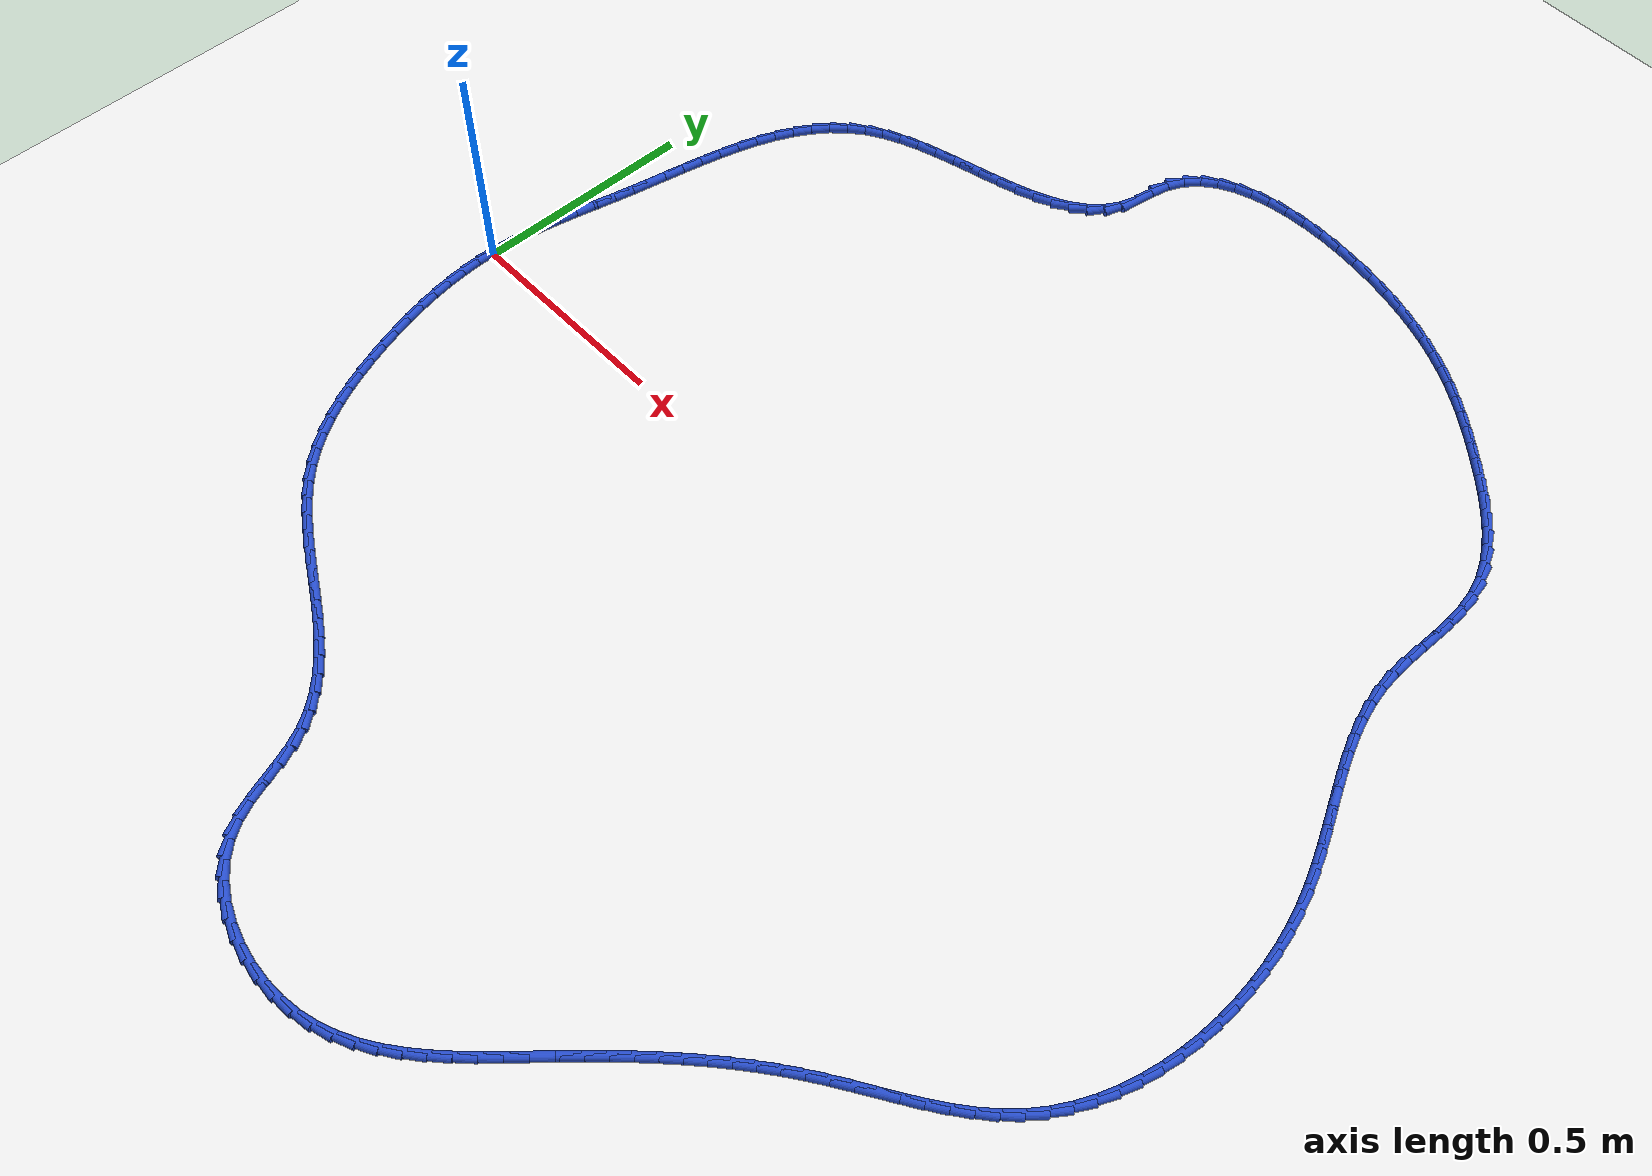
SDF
<sdf version="1.6">
 <world name="default">
  <light name="sun" type="directional">
   <pose>0 0 10 0 -0 0</pose>
   <diffuse>0.8 0.8 0.8 1</diffuse>
   <specular>0.2 0.2 0.2 1</specular>
   <attenuation>
    <range>1000</range>
    <constant>0.9</constant>
    <linear>0.01</linear>
    <quadratic>0.001</quadratic>
   </attenuation>
   <direction>-0.5 0.1 -0.9</direction>
  </light>
  <model name="ground_plane">
   <static>1</static>
   <link name="link">
    <collision name="collision">
     <geometry><plane><normal>0 0 1</normal><size>100 100</size></plane></geometry>
     <surface><friction><ode><mu>100</mu><mu2>50</mu2></ode></friction></surface>
    </collision>
    <visual name="visual">
     <cast_shadows>0</cast_shadows>
     <geometry><plane><normal>0 0 1</normal><size>100 100</size></plane></geometry>
     <material>
      <script><uri>file://media/materials/scripts/gazebo.material</uri><name>Gazebo/WhiteGlow</name></script>
     </material>
    </visual>
   </link>
  </model>
  <gravity>0 0 -9.8</gravity>
  <magnetic_field>6e-06 2.3e-05 -4.2e-05</magnetic_field>
  <atmosphere type="adiabatic"/>
  <physics name="default_physics" default="0" type="ode">
   <max_step_size>0.001</max_step_size>
   <real_time_factor>1</real_time_factor>
   <real_time_update_rate>1000</real_time_update_rate>
  </physics>
  <scene><ambient>0.4 0.4 0.4 1</ambient><background>0.7 0.7 0.7 1</background><shadows>1</shadows></scene>
  <spherical_coordinates>
   <surface_model>EARTH_WGS84</surface_model>
   <latitude_deg>0</latitude_deg>
   <longitude_deg>0</longitude_deg>
   <elevation>0</elevation>
   <heading_deg>0</heading_deg>
  </spherical_coordinates>
  <model name="line">
   <link name="link_0">
    <pose>1.734723475976807e-18 9.71445146547012e-17 0.01 0 1.57 1.5118925620704657</pose>
    <collision name="collision">
     <geometry><cylinder><radius>0.01</radius><length>0.08</length></cylinder></geometry>
    </collision>
    <visual name="visual">
     <material>
      <script><name>Gazebo/Blue</name><uri>file://media/materials/scripts/gazebo.material</uri></script>
     </material>
     <geometry><cylinder><radius>0.01</radius><length>0.08</length></cylinder></geometry>
    </visual>
   </link>
   <link name="link_1">
    <pose>0.002440601395666703 0.04138577684380926 0.01 0 1.57 1.4592444443070107</pose>
    <collision name="collision">
     <geometry><cylinder><radius>0.01</radius><length>0.08</length></cylinder></geometry>
    </collision>
    <visual name="visual">
     <material>
      <script><name>Gazebo/Blue</name><uri>file://media/materials/scripts/gazebo.material</uri></script>
     </material>
     <geometry><cylinder><radius>0.01</radius><length>0.08</length></cylinder></geometry>
    </visual>
   </link>
   <link name="link_2">
    <pose>0.007056655684240985 0.08259432629118585 0.01 0 1.57 1.4165258033613233</pose>
    <collision name="collision">
     <geometry><cylinder><radius>0.01</radius><length>0.08</length></cylinder></geometry>
    </collision>
    <visual name="visual">
     <material>
      <script><name>Gazebo/Blue</name><uri>file://media/materials/scripts/gazebo.material</uri></script>
     </material>
     <geometry><cylinder><radius>0.01</radius><length>0.08</length></cylinder></geometry>
    </visual>
   </link>
   <link name="link_3">
    <pose>0.013461327831780188 0.12378030337710803 0.01 0 1.57 1.3840618345977151</pose>
    <collision name="collision">
     <geometry><cylinder><radius>0.01</radius><length>0.08</length></cylinder></geometry>
    </collision>
    <visual name="visual">
     <material>
      <script><name>Gazebo/Blue</name><uri>file://media/materials/scripts/gazebo.material</uri></script>
     </material>
     <geometry><cylinder><radius>0.01</radius><length>0.08</length></cylinder></geometry>
    </visual>
   </link>
   <link name="link_4">
    <pose>0.021267782804341676 0.16509836313655407 0.01 0 1.57 1.3618621066158823</pose>
    <collision name="collision">
     <geometry><cylinder><radius>0.01</radius><length>0.08</length></cylinder></geometry>
    </collision>
    <visual name="visual">
     <material>
      <script><name>Gazebo/Blue</name><uri>file://media/materials/scripts/gazebo.material</uri></script>
     </material>
     <geometry><cylinder><radius>0.01</radius><length>0.08</length></cylinder></geometry>
    </visual>
   </link>
   <link name="link_5">
    <pose>0.0300891855679828 0.206703160604502 0.01 0 1.57 1.3497281308252556</pose>
    <collision name="collision">
     <geometry><cylinder><radius>0.01</radius><length>0.08</length></cylinder></geometry>
    </collision>
    <visual name="visual">
     <material>
      <script><name>Gazebo/Blue</name><uri>file://media/materials/scripts/gazebo.material</uri></script>
     </material>
     <geometry><cylinder><radius>0.01</radius><length>0.08</length></cylinder></geometry>
    </visual>
   </link>
   <link name="link_6">
    <pose>0.03953870108876091 0.24874935081593003 0.01 0 1.57 1.3473336510708016</pose>
    <collision name="collision">
     <geometry><cylinder><radius>0.01</radius><length>0.08</length></cylinder></geometry>
    </collision>
    <visual name="visual">
     <material>
      <script><name>Gazebo/Blue</name><uri>file://media/materials/scripts/gazebo.material</uri></script>
     </material>
     <geometry><cylinder><radius>0.01</radius><length>0.08</length></cylinder></geometry>
    </visual>
   </link>
   <link name="link_7">
    <pose>0.049229494332733374 0.2913915888058165 0.01 0 1.57 1.354272642317846</pose>
    <collision name="collision">
     <geometry><cylinder><radius>0.01</radius><length>0.08</length></cylinder></geometry>
    </collision>
    <visual name="visual">
     <material>
      <script><name>Gazebo/Blue</name><uri>file://media/materials/scripts/gazebo.material</uri></script>
     </material>
     <geometry><cylinder><radius>0.01</radius><length>0.08</length></cylinder></geometry>
    </visual>
   </link>
   <link name="link_8">
    <pose>0.058774730265957524 0.33478452960913946 0.01 0 1.57 1.3681830134863464</pose>
    <collision name="collision">
     <geometry><cylinder><radius>0.01</radius><length>0.08</length></cylinder></geometry>
    </collision>
    <visual name="visual">
     <material>
      <script><name>Gazebo/Blue</name><uri>file://media/materials/scripts/gazebo.material</uri></script>
     </material>
     <geometry><cylinder><radius>0.01</radius><length>0.08</length></cylinder></geometry>
    </visual>
   </link>
   <link name="link_9">
    <pose>0.06786421708791056 0.3790302108305726 0.01 0 1.57 1.376412043853948</pose>
    <collision name="collision">
     <geometry><cylinder><radius>0.01</radius><length>0.08</length></cylinder></geometry>
    </collision>
    <visual name="visual">
     <material>
      <script><name>Gazebo/Blue</name><uri>file://media/materials/scripts/gazebo.material</uri></script>
     </material>
     <geometry><cylinder><radius>0.01</radius><length>0.08</length></cylinder></geometry>
    </visual>
   </link>
   <link name="link_10">
    <pose>0.07669436747697209 0.42388287386798773 0.01 0 1.57 1.3742911222290082</pose>
    <collision name="collision">
     <geometry><cylinder><radius>0.01</radius><length>0.08</length></cylinder></geometry>
    </collision>
    <visual name="visual">
     <material>
      <script><name>Gazebo/Blue</name><uri>file://media/materials/scripts/gazebo.material</uri></script>
     </material>
     <geometry><cylinder><radius>0.01</radius><length>0.08</length></cylinder></geometry>
    </visual>
   </link>
   <link name="link_11">
    <pose>0.08566718723445407 0.46895561547628856 0.01 0 1.57 1.361929538733073</pose>
    <collision name="collision">
     <geometry><cylinder><radius>0.01</radius><length>0.08</length></cylinder></geometry>
    </collision>
    <visual name="visual">
     <material>
      <script><name>Gazebo/Blue</name><uri>file://media/materials/scripts/gazebo.material</uri></script>
     </material>
     <geometry><cylinder><radius>0.01</radius><length>0.08</length></cylinder></geometry>
    </visual>
   </link>
   <link name="link_12">
    <pose>0.09518527146455512 0.5138611278397183 0.01 0 1.57 1.339055843428847</pose>
    <collision name="collision">
     <geometry><cylinder><radius>0.01</radius><length>0.08</length></cylinder></geometry>
    </collision>
    <visual name="visual">
     <material>
      <script><name>Gazebo/Blue</name><uri>file://media/materials/scripts/gazebo.material</uri></script>
     </material>
     <geometry><cylinder><radius>0.01</radius><length>0.08</length></cylinder></geometry>
    </visual>
   </link>
   <link name="link_13">
    <pose>0.10565121527147389 0.5582121031425203 0.01 0 1.57 1.3050258217924686</pose>
    <collision name="collision">
     <geometry><cylinder><radius>0.01</radius><length>0.08</length></cylinder></geometry>
    </collision>
    <visual name="visual">
     <material>
      <script><name>Gazebo/Blue</name><uri>file://media/materials/scripts/gazebo.material</uri></script>
     </material>
     <geometry><cylinder><radius>0.01</radius><length>0.08</length></cylinder></geometry>
    </visual>
   </link>
   <link name="link_14">
    <pose>0.117467613759409 0.6016212335689382 0.01 0 1.57 1.2588561935308358</pose>
    <collision name="collision">
     <geometry><cylinder><radius>0.01</radius><length>0.08</length></cylinder></geometry>
    </collision>
    <visual name="visual">
     <material>
      <script><name>Gazebo/Blue</name><uri>file://media/materials/scripts/gazebo.material</uri></script>
     </material>
     <geometry><cylinder><radius>0.01</radius><length>0.08</length></cylinder></geometry>
    </visual>
   </link>
   <link name="link_15">
    <pose>0.13103706203255916 0.6437012113032147 0.01 0 1.57 1.1992989600634782</pose>
    <collision name="collision">
     <geometry><cylinder><radius>0.01</radius><length>0.08</length></cylinder></geometry>
    </collision>
    <visual name="visual">
     <material>
      <script><name>Gazebo/Blue</name><uri>file://media/materials/scripts/gazebo.material</uri></script>
     </material>
     <geometry><cylinder><radius>0.01</radius><length>0.08</length></cylinder></geometry>
    </visual>
   </link>
   <link name="link_16">
    <pose>0.14676215519512287 0.6840647285295934 0.01 0 1.57 1.125005807170459</pose>
    <collision name="collision">
     <geometry><cylinder><radius>0.01</radius><length>0.08</length></cylinder></geometry>
    </collision>
    <visual name="visual">
     <material>
      <script><name>Gazebo/Blue</name><uri>file://media/materials/scripts/gazebo.material</uri></script>
     </material>
     <geometry><cylinder><radius>0.01</radius><length>0.08</length></cylinder></geometry>
    </visual>
   </link>
   <link name="link_17">
    <pose>0.1650454883512989 0.7223244774323179 0.01 0 1.57 1.0348503538678946</pose>
    <collision name="collision">
     <geometry><cylinder><radius>0.01</radius><length>0.08</length></cylinder></geometry>
    </collision>
    <visual name="visual">
     <material>
      <script><name>Gazebo/Blue</name><uri>file://media/materials/scripts/gazebo.material</uri></script>
     </material>
     <geometry><cylinder><radius>0.01</radius><length>0.08</length></cylinder></geometry>
    </visual>
   </link>
   <link name="link_18">
    <pose>0.18628965660528587 0.7580931501956311 0.01 0 1.57 0.9284660616330688</pose>
    <collision name="collision">
     <geometry><cylinder><radius>0.01</radius><length>0.08</length></cylinder></geometry>
    </collision>
    <visual name="visual">
     <material>
      <script><name>Gazebo/Blue</name><uri>file://media/materials/scripts/gazebo.material</uri></script>
     </material>
     <geometry><cylinder><radius>0.01</radius><length>0.08</length></cylinder></geometry>
    </visual>
   </link>
   <link name="link_19">
    <pose>0.21089725506128232 0.7909834390037763 0.01 0 1.57 0.806963985858658</pose>
    <collision name="collision">
     <geometry><cylinder><radius>0.01</radius><length>0.08</length></cylinder></geometry>
    </collision>
    <visual name="visual">
     <material>
      <script><name>Gazebo/Blue</name><uri>file://media/materials/scripts/gazebo.material</uri></script>
     </material>
     <geometry><cylinder><radius>0.01</radius><length>0.08</length></cylinder></geometry>
    </visual>
   </link>
   <link name="link_20">
    <pose>0.23927087882348702 0.820608036040997 0.01 0 1.57 0.673574430281032</pose>
    <collision name="collision">
     <geometry><cylinder><radius>0.01</radius><length>0.08</length></cylinder></geometry>
    </collision>
    <visual name="visual">
     <material>
      <script><name>Gazebo/Blue</name><uri>file://media/materials/scripts/gazebo.material</uri></script>
     </material>
     <geometry><cylinder><radius>0.01</radius><length>0.08</length></cylinder></geometry>
    </visual>
   </link>
   <link name="link_21">
    <pose>0.2718131229960985 0.8465796334915365 0.01 0 1.57 0.5373420039086666</pose>
    <collision name="collision">
     <geometry><cylinder><radius>0.01</radius><length>0.08</length></cylinder></geometry>
    </collision>
    <visual name="visual">
     <material>
      <script><name>Gazebo/Blue</name><uri>file://media/materials/scripts/gazebo.material</uri></script>
     </material>
     <geometry><cylinder><radius>0.01</radius><length>0.08</length></cylinder></geometry>
    </visual>
   </link>
   <link name="link_22">
    <pose>0.30880189917166323 0.8686183714034724 0.01 0 1.57 0.4254899743307072</pose>
    <collision name="collision">
     <geometry><cylinder><radius>0.01</radius><length>0.08</length></cylinder></geometry>
    </collision>
    <visual name="visual">
     <material>
      <script><name>Gazebo/Blue</name><uri>file://media/materials/scripts/gazebo.material</uri></script>
     </material>
     <geometry><cylinder><radius>0.01</radius><length>0.08</length></cylinder></geometry>
    </visual>
   </link>
   <link name="link_23">
    <pose>0.34969583162918266 0.8871504228082355 0.01 0 1.57 0.34399910165057807</pose>
    <collision name="collision">
     <geometry><cylinder><radius>0.01</radius><length>0.08</length></cylinder></geometry>
    </collision>
    <visual name="visual">
     <material>
      <script><name>Gazebo/Blue</name><uri>file://media/materials/scripts/gazebo.material</uri></script>
     </material>
     <geometry><cylinder><radius>0.01</radius><length>0.08</length></cylinder></geometry>
    </visual>
   </link>
   <link name="link_24">
    <pose>0.3936228348866499 0.9028869547745484 0.01 0 1.57 0.2880064697864589</pose>
    <collision name="collision">
     <geometry><cylinder><radius>0.01</radius><length>0.08</length></cylinder></geometry>
    </collision>
    <visual name="visual">
     <material>
      <script><name>Gazebo/Blue</name><uri>file://media/materials/scripts/gazebo.material</uri></script>
     </material>
     <geometry><cylinder><radius>0.01</radius><length>0.08</length></cylinder></geometry>
    </visual>
   </link>
   <link name="link_25">
    <pose>0.43970990349803835 0.9165399271637614 0.01 0 1.57 0.25365809883870455</pose>
    <collision name="collision">
     <geometry><cylinder><radius>0.01</radius><length>0.08</length></cylinder></geometry>
    </collision>
    <visual name="visual">
     <material>
      <script><name>Gazebo/Blue</name><uri>file://media/materials/scripts/gazebo.material</uri></script>
     </material>
     <geometry><cylinder><radius>0.01</radius><length>0.08</length></cylinder></geometry>
    </visual>
   </link>
   <link name="link_26">
    <pose>0.48708403201732026 0.928821299837224 0.01 0 1.57 0.23856151467213263</pose>
    <collision name="collision">
     <geometry><cylinder><radius>0.01</radius><length>0.08</length></cylinder></geometry>
    </collision>
    <visual name="visual">
     <material>
      <script><name>Gazebo/Blue</name><uri>file://media/materials/scripts/gazebo.material</uri></script>
     </material>
     <geometry><cylinder><radius>0.01</radius><length>0.08</length></cylinder></geometry>
    </visual>
   </link>
   <link name="link_27">
    <pose>0.5348722149984687 0.9404430326562868 0.01 0 1.57 0.24182917553623962</pose>
    <collision name="collision">
     <geometry><cylinder><radius>0.01</radius><length>0.08</length></cylinder></geometry>
    </collision>
    <visual name="visual">
     <material>
      <script><name>Gazebo/Blue</name><uri>file://media/materials/scripts/gazebo.material</uri></script>
     </material>
     <geometry><cylinder><radius>0.01</radius><length>0.08</length></cylinder></geometry>
    </visual>
   </link>
   <link name="link_28">
    <pose>0.5822014469954565 0.9521170854822995 0.01 0 1.57 0.26409817928467055</pose>
    <collision name="collision">
     <geometry><cylinder><radius>0.01</radius><length>0.08</length></cylinder></geometry>
    </collision>
    <visual name="visual">
     <material>
      <script><name>Gazebo/Blue</name><uri>file://media/materials/scripts/gazebo.material</uri></script>
     </material>
     <geometry><cylinder><radius>0.01</radius><length>0.08</length></cylinder></geometry>
    </visual>
   </link>
   <link name="link_29">
    <pose>0.6281987225622563 0.9645554181766117 0.01 0 1.57 0.3076515844914948</pose>
    <collision name="collision">
     <geometry><cylinder><radius>0.01</radius><length>0.08</length></cylinder></geometry>
    </collision>
    <visual name="visual">
     <material>
      <script><name>Gazebo/Blue</name><uri>file://media/materials/scripts/gazebo.material</uri></script>
     </material>
     <geometry><cylinder><radius>0.01</radius><length>0.08</length></cylinder></geometry>
    </visual>
   </link>
   <link name="link_30">
    <pose>0.6719910362528413 0.9784699906005743 0.01 0 1.57 0.3766263251963658</pose>
    <collision name="collision">
     <geometry><cylinder><radius>0.01</radius><length>0.08</length></cylinder></geometry>
    </collision>
    <visual name="visual">
     <material>
      <script><name>Gazebo/Blue</name><uri>file://media/materials/scripts/gazebo.material</uri></script>
     </material>
     <geometry><cylinder><radius>0.01</radius><length>0.08</length></cylinder></geometry>
    </visual>
   </link>
   <link name="link_31">
    <pose>0.7127053826211839 0.9945727626155364 0.01 0 1.57 0.4770748107611785</pose>
    <collision name="collision">
     <geometry><cylinder><radius>0.01</radius><length>0.08</length></cylinder></geometry>
    </collision>
    <visual name="visual">
     <material>
      <script><name>Gazebo/Blue</name><uri>file://media/materials/scripts/gazebo.material</uri></script>
     </material>
     <geometry><cylinder><radius>0.01</radius><length>0.08</length></cylinder></geometry>
    </visual>
   </link>
   <link name="link_32">
    <pose>0.749468756221257 1.0135756940828482 0.01 0 1.57 0.6161157883373141</pose>
    <collision name="collision">
     <geometry><cylinder><radius>0.01</radius><length>0.08</length></cylinder></geometry>
    </collision>
    <visual name="visual">
     <material>
      <script><name>Gazebo/Blue</name><uri>file://media/materials/scripts/gazebo.material</uri></script>
     </material>
     <geometry><cylinder><radius>0.01</radius><length>0.08</length></cylinder></geometry>
    </visual>
   </link>
   <link name="link_33">
    <pose>0.7814081516070338 1.03619074486386 0.01 0 1.57 0.7984981667726718</pose>
    <collision name="collision">
     <geometry><cylinder><radius>0.01</radius><length>0.08</length></cylinder></geometry>
    </collision>
    <visual name="visual">
     <material>
      <script><name>Gazebo/Blue</name><uri>file://media/materials/scripts/gazebo.material</uri></script>
     </material>
     <geometry><cylinder><radius>0.01</radius><length>0.08</length></cylinder></geometry>
    </visual>
   </link>
   <link name="link_34">
    <pose>0.8076505633324866 1.063129874819922 0.01 0 1.57 1.0192457979860359</pose>
    <collision name="collision">
     <geometry><cylinder><radius>0.01</radius><length>0.08</length></cylinder></geometry>
    </collision>
    <visual name="visual">
     <material>
      <script><name>Gazebo/Blue</name><uri>file://media/materials/scripts/gazebo.material</uri></script>
     </material>
     <geometry><cylinder><radius>0.01</radius><length>0.08</length></cylinder></geometry>
    </visual>
   </link>
   <link name="link_35">
    <pose>0.8273229859515889 1.095105043812384 0.01 0 1.57 1.2571919003249752</pose>
    <collision name="collision">
     <geometry><cylinder><radius>0.01</radius><length>0.08</length></cylinder></geometry>
    </collision>
    <visual name="visual">
     <material>
      <script><name>Gazebo/Blue</name><uri>file://media/materials/scripts/gazebo.material</uri></script>
     </material>
     <geometry><cylinder><radius>0.01</radius><length>0.08</length></cylinder></geometry>
    </visual>
   </link>
   <link name="link_36">
    <pose>0.8395559789018703 1.132825524364342 0.01 0 1.57 1.421813403696601</pose>
    <collision name="collision">
     <geometry><cylinder><radius>0.01</radius><length>0.08</length></cylinder></geometry>
    </collision>
    <visual name="visual">
     <material>
      <script><name>Gazebo/Blue</name><uri>file://media/materials/scripts/gazebo.material</uri></script>
     </material>
     <geometry><cylinder><radius>0.01</radius><length>0.08</length></cylinder></geometry>
    </visual>
   </link>
   <link name="link_37">
    <pose>0.8459113496168702 1.1751678262624599 0.01 0 1.57 1.3623700531676382</pose>
    <collision name="collision">
     <geometry><cylinder><radius>0.01</radius><length>0.08</length></cylinder></geometry>
    </collision>
    <visual name="visual">
     <material>
      <script><name>Gazebo/Blue</name><uri>file://media/materials/scripts/gazebo.material</uri></script>
     </material>
     <geometry><cylinder><radius>0.01</radius><length>0.08</length></cylinder></geometry>
    </visual>
   </link>
   <link name="link_38">
    <pose>0.8545534360814249 1.2160291851540015 0.01 0 1.57 1.131603148136454</pose>
    <collision name="collision">
     <geometry><cylinder><radius>0.01</radius><length>0.08</length></cylinder></geometry>
    </collision>
    <visual name="visual">
     <material>
      <script><name>Gazebo/Blue</name><uri>file://media/materials/scripts/gazebo.material</uri></script>
     </material>
     <geometry><cylinder><radius>0.01</radius><length>0.08</length></cylinder></geometry>
    </visual>
   </link>
   <link name="link_39">
    <pose>0.8710465919229426 1.2511362992995012 0.01 0 1.57 0.8850576071320237</pose>
    <collision name="collision">
     <geometry><cylinder><radius>0.01</radius><length>0.08</length></cylinder></geometry>
    </collision>
    <visual name="visual">
     <material>
      <script><name>Gazebo/Blue</name><uri>file://media/materials/scripts/gazebo.material</uri></script>
     </material>
     <geometry><cylinder><radius>0.01</radius><length>0.08</length></cylinder></geometry>
    </visual>
   </link>
   <link name="link_40">
    <pose>0.8950436015195598 1.280465426609109 0.01 0 1.57 0.6626870986300039</pose>
    <collision name="collision">
     <geometry><cylinder><radius>0.01</radius><length>0.08</length></cylinder></geometry>
    </collision>
    <visual name="visual">
     <material>
      <script><name>Gazebo/Blue</name><uri>file://media/materials/scripts/gazebo.material</uri></script>
     </material>
     <geometry><cylinder><radius>0.01</radius><length>0.08</length></cylinder></geometry>
    </visual>
   </link>
   <link name="link_41">
    <pose>0.925673317251399 1.3043694559997367 0.01 0 1.57 0.47753500186646297</pose>
    <collision name="collision">
     <geometry><cylinder><radius>0.01</radius><length>0.08</length></cylinder></geometry>
    </collision>
    <visual name="visual">
     <material>
      <script><name>Gazebo/Blue</name><uri>file://media/materials/scripts/gazebo.material</uri></script>
     </material>
     <geometry><cylinder><radius>0.01</radius><length>0.08</length></cylinder></geometry>
    </visual>
   </link>
   <link name="link_42">
    <pose>0.9620645914985838 1.323201276388297 0.01 0 1.57 0.3294035977487588</pose>
    <collision name="collision">
     <geometry><cylinder><radius>0.01</radius><length>0.08</length></cylinder></geometry>
    </collision>
    <visual name="visual">
     <material>
      <script><name>Gazebo/Blue</name><uri>file://media/materials/scripts/gazebo.material</uri></script>
     </material>
     <geometry><cylinder><radius>0.01</radius><length>0.08</length></cylinder></geometry>
    </visual>
   </link>
   <link name="link_43">
    <pose>1.0033462766412369 1.3373137766917018 0.01 0 1.57 0.2119104578036931</pose>
    <collision name="collision">
     <geometry><cylinder><radius>0.01</radius><length>0.08</length></cylinder></geometry>
    </collision>
    <visual name="visual">
     <material>
      <script><name>Gazebo/Blue</name><uri>file://media/materials/scripts/gazebo.material</uri></script>
     </material>
     <geometry><cylinder><radius>0.01</radius><length>0.08</length></cylinder></geometry>
    </visual>
   </link>
   <link name="link_44">
    <pose>1.0486472250594814 1.3470598458268634 0.01 0 1.57 0.11777313130490023</pose>
    <collision name="collision">
     <geometry><cylinder><radius>0.01</radius><length>0.08</length></cylinder></geometry>
    </collision>
    <visual name="visual">
     <material>
      <script><name>Gazebo/Blue</name><uri>file://media/materials/scripts/gazebo.material</uri></script>
     </material>
     <geometry><cylinder><radius>0.01</radius><length>0.08</length></cylinder></geometry>
    </visual>
   </link>
   <link name="link_45">
    <pose>1.0970962891334404 1.3527923727106943 0.01 0 1.57 0.04082169393762994</pose>
    <collision name="collision">
     <geometry><cylinder><radius>0.01</radius><length>0.08</length></cylinder></geometry>
    </collision>
    <visual name="visual">
     <material>
      <script><name>Gazebo/Blue</name><uri>file://media/materials/scripts/gazebo.material</uri></script>
     </material>
     <geometry><cylinder><radius>0.01</radius><length>0.08</length></cylinder></geometry>
    </visual>
   </link>
   <link name="link_46">
    <pose>1.147822321243237 1.3548642462601064 0.01 0 1.57 -0.023702580156370844</pose>
    <collision name="collision">
     <geometry><cylinder><radius>0.01</radius><length>0.08</length></cylinder></geometry>
    </collision>
    <visual name="visual">
     <material>
      <script><name>Gazebo/Blue</name><uri>file://media/materials/scripts/gazebo.material</uri></script>
     </material>
     <geometry><cylinder><radius>0.01</radius><length>0.08</length></cylinder></geometry>
    </visual>
   </link>
   <link name="link_47">
    <pose>1.1999541737689943 1.3536283553920125 0.01 0 1.57 -0.07940442164863164</pose>
    <collision name="collision">
     <geometry><cylinder><radius>0.01</radius><length>0.08</length></cylinder></geometry>
    </collision>
    <visual name="visual">
     <material>
      <script><name>Gazebo/Blue</name><uri>file://media/materials/scripts/gazebo.material</uri></script>
     </material>
     <geometry><cylinder><radius>0.01</radius><length>0.08</length></cylinder></geometry>
    </visual>
   </link>
   <link name="link_48">
    <pose>1.252620699090835 1.3494375890233241 0.01 0 1.57 -0.12908419369028848</pose>
    <collision name="collision">
     <geometry><cylinder><radius>0.01</radius><length>0.08</length></cylinder></geometry>
    </collision>
    <visual name="visual">
     <material>
      <script><name>Gazebo/Blue</name><uri>file://media/materials/scripts/gazebo.material</uri></script>
     </material>
     <geometry><cylinder><radius>0.01</radius><length>0.08</length></cylinder></geometry>
    </visual>
   </link>
   <link name="link_49">
    <pose>1.3049507495888832 1.342644836070954 0.01 0 1.57 -0.17505623574425683</pose>
    <collision name="collision">
     <geometry><cylinder><radius>0.01</radius><length>0.08</length></cylinder></geometry>
    </collision>
    <visual name="visual">
     <material>
      <script><name>Gazebo/Blue</name><uri>file://media/materials/scripts/gazebo.material</uri></script>
     </material>
     <geometry><cylinder><radius>0.01</radius><length>0.08</length></cylinder></geometry>
    </visual>
   </link>
   <link name="link_50">
    <pose>1.3560731776432606 1.3336029854518143 0.01 0 1.57 -0.21943573415509873</pose>
    <collision name="collision">
     <geometry><cylinder><radius>0.01</radius><length>0.08</length></cylinder></geometry>
    </collision>
    <visual name="visual">
     <material>
      <script><name>Gazebo/Blue</name><uri>file://media/materials/scripts/gazebo.material</uri></script>
     </material>
     <geometry><cylinder><radius>0.01</radius><length>0.08</length></cylinder></geometry>
    </visual>
   </link>
   <link name="link_51">
    <pose>1.4051168564127836 1.3226649202259875 0.01 0 1.57 -0.2644905807101352</pose>
    <collision name="collision">
     <geometry><cylinder><radius>0.01</radius><length>0.08</length></cylinder></geometry>
    </collision>
    <visual name="visual">
     <material>
      <script><name>Gazebo/Blue</name><uri>file://media/materials/scripts/gazebo.material</uri></script>
     </material>
     <geometry><cylinder><radius>0.01</radius><length>0.08</length></cylinder></geometry>
    </visual>
   </link>
   <link name="link_52">
    <pose>1.451432769603472 1.3101209177924598 0.01 0 1.57 -0.311564526251264</pose>
    <collision name="collision">
     <geometry><cylinder><radius>0.01</radius><length>0.08</length></cylinder></geometry>
    </collision>
    <visual name="visual">
     <material>
      <script><name>Gazebo/Blue</name><uri>file://media/materials/scripts/gazebo.material</uri></script>
     </material>
     <geometry><cylinder><radius>0.01</radius><length>0.08</length></cylinder></geometry>
    </visual>
   </link>
   <link name="link_53">
    <pose>1.49514250113705 1.2960440486838574 0.01 0 1.57 -0.36007658148375093</pose>
    <collision name="collision">
     <geometry><cylinder><radius>0.01</radius><length>0.08</length></cylinder></geometry>
    </collision>
    <visual name="visual">
     <material>
      <script><name>Gazebo/Blue</name><uri>file://media/materials/scripts/gazebo.material</uri></script>
     </material>
     <geometry><cylinder><radius>0.01</radius><length>0.08</length></cylinder></geometry>
    </visual>
   </link>
   <link name="link_54">
    <pose>1.5365346432173967 1.2804603092886733 0.01 0 1.57 -0.4090628946613508</pose>
    <collision name="collision">
     <geometry><cylinder><radius>0.01</radius><length>0.08</length></cylinder></geometry>
    </collision>
    <visual name="visual">
     <material>
      <script><name>Gazebo/Blue</name><uri>file://media/materials/scripts/gazebo.material</uri></script>
     </material>
     <geometry><cylinder><radius>0.01</radius><length>0.08</length></cylinder></geometry>
    </visual>
   </link>
   <link name="link_55">
    <pose>1.5758977880483918 1.2633956959954 0.01 0 1.57 -0.4574219296724204</pose>
    <collision name="collision">
     <geometry><cylinder><radius>0.01</radius><length>0.08</length></cylinder></geometry>
    </collision>
    <visual name="visual">
     <material>
      <script><name>Gazebo/Blue</name><uri>file://media/materials/scripts/gazebo.material</uri></script>
     </material>
     <geometry><cylinder><radius>0.01</radius><length>0.08</length></cylinder></geometry>
    </visual>
   </link>
   <link name="link_56">
    <pose>1.6135205278339109 1.2448762051925306 0.01 0 1.57 -0.5039963539387889</pose>
    <collision name="collision">
     <geometry><cylinder><radius>0.01</radius><length>0.08</length></cylinder></geometry>
    </collision>
    <visual name="visual">
     <material>
      <script><name>Gazebo/Blue</name><uri>file://media/materials/scripts/gazebo.material</uri></script>
     </material>
     <geometry><cylinder><radius>0.01</radius><length>0.08</length></cylinder></geometry>
    </visual>
   </link>
   <link name="link_57">
    <pose>1.6496914547778343 1.2249278332685578 0.01 0 1.57 -0.5476683075170772</pose>
    <collision name="collision">
     <geometry><cylinder><radius>0.01</radius><length>0.08</length></cylinder></geometry>
    </collision>
    <visual name="visual">
     <material>
      <script><name>Gazebo/Blue</name><uri>file://media/materials/scripts/gazebo.material</uri></script>
     </material>
     <geometry><cylinder><radius>0.01</radius><length>0.08</length></cylinder></geometry>
    </visual>
   </link>
   <link name="link_58">
    <pose>1.6846991610840407 1.2035765766119741 0.01 0 1.57 -0.5874498968761576</pose>
    <collision name="collision">
     <geometry><cylinder><radius>0.01</radius><length>0.08</length></cylinder></geometry>
    </collision>
    <visual name="visual">
     <material>
      <script><name>Gazebo/Blue</name><uri>file://media/materials/scripts/gazebo.material</uri></script>
     </material>
     <geometry><cylinder><radius>0.01</radius><length>0.08</length></cylinder></geometry>
    </visual>
   </link>
   <link name="link_59">
    <pose>1.7188322389564075 1.180848431611273 0.01 0 1.57 -0.6225523932730951</pose>
    <collision name="collision">
     <geometry><cylinder><radius>0.01</radius><length>0.08</length></cylinder></geometry>
    </collision>
    <visual name="visual">
     <material>
      <script><name>Gazebo/Blue</name><uri>file://media/materials/scripts/gazebo.material</uri></script>
     </material>
     <geometry><cylinder><radius>0.01</radius><length>0.08</length></cylinder></geometry>
    </visual>
   </link>
   <link name="link_60">
    <pose>1.7523792805988143 1.1567693946549467 0.01 0 1.57 -0.6524246115541976</pose>
    <collision name="collision">
     <geometry><cylinder><radius>0.01</radius><length>0.08</length></cylinder></geometry>
    </collision>
    <visual name="visual">
     <material>
      <script><name>Gazebo/Blue</name><uri>file://media/materials/scripts/gazebo.material</uri></script>
     </material>
     <geometry><cylinder><radius>0.01</radius><length>0.08</length></cylinder></geometry>
    </visual>
   </link>
   <link name="link_61">
    <pose>1.7856288782151375 1.1313654621314881 0.01 0 1.57 -0.6767597854101373</pose>
    <collision name="collision">
     <geometry><cylinder><radius>0.01</radius><length>0.08</length></cylinder></geometry>
    </collision>
    <visual name="visual">
     <material>
      <script><name>Gazebo/Blue</name><uri>file://media/materials/scripts/gazebo.material</uri></script>
     </material>
     <geometry><cylinder><radius>0.01</radius><length>0.08</length></cylinder></geometry>
    </visual>
   </link>
   <link name="link_62">
    <pose>1.8188696240092572 1.1046626304293907 0.01 0 1.57 -0.6976279733830066</pose>
    <collision name="collision">
     <geometry><cylinder><radius>0.01</radius><length>0.08</length></cylinder></geometry>
    </collision>
    <visual name="visual">
     <material>
      <script><name>Gazebo/Blue</name><uri>file://media/materials/scripts/gazebo.material</uri></script>
     </material>
     <geometry><cylinder><radius>0.01</radius><length>0.08</length></cylinder></geometry>
    </visual>
   </link>
   <link name="link_63">
    <pose>1.8522595238247823 1.0766738274564027 0.01 0 1.57 -0.7270384417598258</pose>
    <collision name="collision">
     <geometry><cylinder><radius>0.01</radius><length>0.08</length></cylinder></geometry>
    </collision>
    <visual name="visual">
     <material>
      <script><name>Gazebo/Blue</name><uri>file://media/materials/scripts/gazebo.material</uri></script>
     </material>
     <geometry><cylinder><radius>0.01</radius><length>0.08</length></cylinder></geometry>
    </visual>
   </link>
   <link name="link_64">
    <pose>1.8852341255256664 1.0473396808572495 0.01 0 1.57 -0.769679246691974</pose>
    <collision name="collision">
     <geometry><cylinder><radius>0.01</radius><length>0.08</length></cylinder></geometry>
    </collision>
    <visual name="visual">
     <material>
      <script><name>Gazebo/Blue</name><uri>file://media/materials/scripts/gazebo.material</uri></script>
     </material>
     <geometry><cylinder><radius>0.01</radius><length>0.08</length></cylinder></geometry>
    </visual>
   </link>
   <link name="link_65">
    <pose>1.9169805244783376 1.0165759542964274 0.01 0 1.57 -0.8268779449244769</pose>
    <collision name="collision">
     <geometry><cylinder><radius>0.01</radius><length>0.08</length></cylinder></geometry>
    </collision>
    <visual name="visual">
     <material>
      <script><name>Gazebo/Blue</name><uri>file://media/materials/scripts/gazebo.material</uri></script>
     </material>
     <geometry><cylinder><radius>0.01</radius><length>0.08</length></cylinder></geometry>
    </visual>
   </link>
   <link name="link_66">
    <pose>1.9466855885977083 0.9842983886761354 0.01 0 1.57 -0.9005703691027044</pose>
    <collision name="collision">
     <geometry><cylinder><radius>0.01</radius><length>0.08</length></cylinder></geometry>
    </collision>
    <visual name="visual">
     <material>
      <script><name>Gazebo/Blue</name><uri>file://media/materials/scripts/gazebo.material</uri></script>
     </material>
     <geometry><cylinder><radius>0.01</radius><length>0.08</length></cylinder></geometry>
    </visual>
   </link>
   <link name="link_67">
    <pose>1.973536185798688 0.9504227248985719 0.01 0 1.57 -0.9930328247931165</pose>
    <collision name="collision">
     <geometry><cylinder><radius>0.01</radius><length>0.08</length></cylinder></geometry>
    </collision>
    <visual name="visual">
     <material>
      <script><name>Gazebo/Blue</name><uri>file://media/materials/scripts/gazebo.material</uri></script>
     </material>
     <geometry><cylinder><radius>0.01</radius><length>0.08</length></cylinder></geometry>
    </visual>
   </link>
   <link name="link_68">
    <pose>1.996719183996188 0.9148647038659359 0.01 0 1.57 -1.1062928474867122</pose>
    <collision name="collision">
     <geometry><cylinder><radius>0.01</radius><length>0.08</length></cylinder></geometry>
    </collision>
    <visual name="visual">
     <material>
      <script><name>Gazebo/Blue</name><uri>file://media/materials/scripts/gazebo.material</uri></script>
     </material>
     <geometry><cylinder><radius>0.01</radius><length>0.08</length></cylinder></geometry>
    </visual>
   </link>
   <link name="link_69">
    <pose>2.0154214511051194 0.8775400664804246 0.01 0 1.57 -1.2408571684491947</pose>
    <collision name="collision">
     <geometry><cylinder><radius>0.01</radius><length>0.08</length></cylinder></geometry>
    </collision>
    <visual name="visual">
     <material>
      <script><name>Gazebo/Blue</name><uri>file://media/materials/scripts/gazebo.material</uri></script>
     </material>
     <geometry><cylinder><radius>0.01</radius><length>0.08</length></cylinder></geometry>
    </visual>
   </link>
   <link name="link_70">
    <pose>2.0288367818500235 0.8383662867435983 0.01 0 1.57 -1.3764013165145574</pose>
    <collision name="collision">
     <geometry><cylinder><radius>0.01</radius><length>0.08</length></cylinder></geometry>
    </collision>
    <visual name="visual">
     <material>
      <script><name>Gazebo/Blue</name><uri>file://media/materials/scripts/gazebo.material</uri></script>
     </material>
     <geometry><cylinder><radius>0.01</radius><length>0.08</length></cylinder></geometry>
    </visual>
   </link>
   <link name="link_71">
    <pose>2.036893492948129 0.797444617288669 0.01 0 1.57 -1.4763379174900986</pose>
    <collision name="collision">
     <geometry><cylinder><radius>0.01</radius><length>0.08</length></cylinder></geometry>
    </collision>
    <visual name="visual">
     <material>
      <script><name>Gazebo/Blue</name><uri>file://media/materials/scripts/gazebo.material</uri></script>
     </material>
     <geometry><cylinder><radius>0.01</radius><length>0.08</length></cylinder></geometry>
    </visual>
   </link>
   <link name="link_72">
    <pose>2.0408938604904856 0.7552200776832422 0.01 0 1.57 -1.5383516902218048</pose>
    <collision name="collision">
     <geometry><cylinder><radius>0.01</radius><length>0.08</length></cylinder></geometry>
    </collision>
    <visual name="visual">
     <material>
      <script><name>Gazebo/Blue</name><uri>file://media/materials/scripts/gazebo.material</uri></script>
     </material>
     <geometry><cylinder><radius>0.01</radius><length>0.08</length></cylinder></geometry>
    </visual>
   </link>
   <link name="link_73">
    <pose>2.042290919408614 0.7121754076090748 0.01 0 1.57 -1.5651077412706345</pose>
    <collision name="collision">
     <geometry><cylinder><radius>0.01</radius><length>0.08</length></cylinder></geometry>
    </collision>
    <visual name="visual">
     <material>
      <script><name>Gazebo/Blue</name><uri>file://media/materials/scripts/gazebo.material</uri></script>
     </material>
     <geometry><cylinder><radius>0.01</radius><length>0.08</length></cylinder></geometry>
    </visual>
   </link>
   <link name="link_74">
    <pose>2.0425377046340376 0.6687933467479239 0.01 0 1.57 -1.5580868294887238</pose>
    <collision name="collision">
     <geometry><cylinder><radius>0.01</radius><length>0.08</length></cylinder></geometry>
    </collision>
    <visual name="visual">
     <material>
      <script><name>Gazebo/Blue</name><uri>file://media/materials/scripts/gazebo.material</uri></script>
     </material>
     <geometry><cylinder><radius>0.01</radius><length>0.08</length></cylinder></geometry>
    </visual>
   </link>
   <link name="link_75">
    <pose>2.0430872510982763 0.6255566347815473 0.01 0 1.57 -1.5167439572859542</pose>
    <collision name="collision">
     <geometry><cylinder><radius>0.01</radius><length>0.08</length></cylinder></geometry>
    </collision>
    <visual name="visual">
     <material>
      <script><name>Gazebo/Blue</name><uri>file://media/materials/scripts/gazebo.material</uri></script>
     </material>
     <geometry><cylinder><radius>0.01</radius><length>0.08</length></cylinder></geometry>
    </visual>
   </link>
   <link name="link_76">
    <pose>2.045392593732852 0.582948011391702 0.01 0 1.57 -1.4398840844736198</pose>
    <collision name="collision">
     <geometry><cylinder><radius>0.01</radius><length>0.08</length></cylinder></geometry>
    </collision>
    <visual name="visual">
     <material>
      <script><name>Gazebo/Blue</name><uri>file://media/materials/scripts/gazebo.material</uri></script>
     </material>
     <geometry><cylinder><radius>0.01</radius><length>0.08</length></cylinder></geometry>
    </visual>
   </link>
   <link name="link_77">
    <pose>2.0508587106441674 0.5414327569881692 0.01 0 1.57 -1.3495234273014156</pose>
    <collision name="collision">
     <geometry><cylinder><radius>0.01</radius><length>0.08</length></cylinder></geometry>
    </collision>
    <visual name="visual">
     <material>
      <script><name>Gazebo/Blue</name><uri>file://media/materials/scripts/gazebo.material</uri></script>
     </material>
     <geometry><cylinder><radius>0.01</radius><length>0.08</length></cylinder></geometry>
    </visual>
   </link>
   <link name="link_78">
    <pose>2.0599260330493103 0.5011257275315094 0.01 0 1.57 -1.2694675093479777</pose>
    <collision name="collision">
     <geometry><cylinder><radius>0.01</radius><length>0.08</length></cylinder></geometry>
    </collision>
    <visual name="visual">
     <material>
      <script><name>Gazebo/Blue</name><uri>file://media/materials/scripts/gazebo.material</uri></script>
     </material>
     <geometry><cylinder><radius>0.01</radius><length>0.08</length></cylinder></geometry>
    </visual>
   </link>
   <link name="link_79">
    <pose>2.0721427137337862 0.46181761000573485 0.01 0 1.57 -1.2022416108094847</pose>
    <collision name="collision">
     <geometry><cylinder><radius>0.01</radius><length>0.08</length></cylinder></geometry>
    </collision>
    <visual name="visual">
     <material>
      <script><name>Gazebo/Blue</name><uri>file://media/materials/scripts/gazebo.material</uri></script>
     </material>
     <geometry><cylinder><radius>0.01</radius><length>0.08</length></cylinder></geometry>
    </visual>
   </link>
   <link name="link_80">
    <pose>2.087023329836767 0.42328689320366225 0.01 0 1.57 -1.1485895569583218</pose>
    <collision name="collision">
     <geometry><cylinder><radius>0.01</radius><length>0.08</length></cylinder></geometry>
    </collision>
    <visual name="visual">
     <material>
      <script><name>Gazebo/Blue</name><uri>file://media/materials/scripts/gazebo.material</uri></script>
     </material>
     <geometry><cylinder><radius>0.01</radius><length>0.08</length></cylinder></geometry>
    </visual>
   </link>
   <link name="link_81">
    <pose>2.104082458497425 0.385312065918109 0.01 0 1.57 -1.108595146155567</pose>
    <collision name="collision">
     <geometry><cylinder><radius>0.01</radius><length>0.08</length></cylinder></geometry>
    </collision>
    <visual name="visual">
     <material>
      <script><name>Gazebo/Blue</name><uri>file://media/materials/scripts/gazebo.material</uri></script>
     </material>
     <geometry><cylinder><radius>0.01</radius><length>0.08</length></cylinder></geometry>
    </visual>
   </link>
   <link name="link_82">
    <pose>2.1228346768549327 0.3476716169418919 0.01 0 1.57 -1.0819770920410037</pose>
    <collision name="collision">
     <geometry><cylinder><radius>0.01</radius><length>0.08</length></cylinder></geometry>
    </collision>
    <visual name="visual">
     <material>
      <script><name>Gazebo/Blue</name><uri>file://media/materials/scripts/gazebo.material</uri></script>
     </material>
     <geometry><cylinder><radius>0.01</radius><length>0.08</length></cylinder></geometry>
    </visual>
   </link>
   <link name="link_83">
    <pose>2.142794562048462 0.3101440350678275 0.01 0 1.57 -1.0683161971109423</pose>
    <collision name="collision">
     <geometry><cylinder><radius>0.01</radius><length>0.08</length></cylinder></geometry>
    </collision>
    <visual name="visual">
     <material>
      <script><name>Gazebo/Blue</name><uri>file://media/materials/scripts/gazebo.material</uri></script>
     </material>
     <geometry><cylinder><radius>0.01</radius><length>0.08</length></cylinder></geometry>
    </visual>
   </link>
   <link name="link_84">
    <pose>2.1634766912171854 0.27250780908873323 0.01 0 1.57 -1.067196309712087</pose>
    <collision name="collision">
     <geometry><cylinder><radius>0.01</radius><length>0.08</length></cylinder></geometry>
    </collision>
    <visual name="visual">
     <material>
      <script><name>Gazebo/Blue</name><uri>file://media/materials/scripts/gazebo.material</uri></script>
     </material>
     <geometry><cylinder><radius>0.01</radius><length>0.08</length></cylinder></geometry>
    </visual>
   </link>
   <link name="link_85">
    <pose>2.1843956415002763 0.23454142779742548 0.01 0 1.57 -1.0782676707081533</pose>
    <collision name="collision">
     <geometry><cylinder><radius>0.01</radius><length>0.08</length></cylinder></geometry>
    </collision>
    <visual name="visual">
     <material>
      <script><name>Gazebo/Blue</name><uri>file://media/materials/scripts/gazebo.material</uri></script>
     </material>
     <geometry><cylinder><radius>0.01</radius><length>0.08</length></cylinder></geometry>
    </visual>
   </link>
   <link name="link_86">
    <pose>2.2050659900369065 0.19602337998672187 0.01 0 1.57 -1.1012471465318383</pose>
    <collision name="collision">
     <geometry><cylinder><radius>0.01</radius><length>0.08</length></cylinder></geometry>
    </collision>
    <visual name="visual">
     <material>
      <script><name>Gazebo/Blue</name><uri>file://media/materials/scripts/gazebo.material</uri></script>
     </material>
     <geometry><cylinder><radius>0.01</radius><length>0.08</length></cylinder></geometry>
    </visual>
   </link>
   <link name="link_87">
    <pose>2.225002313966249 0.15673215444943892 0.01 0 1.57 -1.135866761905109</pose>
    <collision name="collision">
     <geometry><cylinder><radius>0.01</radius><length>0.08</length></cylinder></geometry>
    </collision>
    <visual name="visual">
     <material>
      <script><name>Gazebo/Blue</name><uri>file://media/materials/scripts/gazebo.material</uri></script>
     </material>
     <geometry><cylinder><radius>0.01</radius><length>0.08</length></cylinder></geometry>
    </visual>
   </link>
   <link name="link_88">
    <pose>2.2437191904274743 0.11644623997839301 0.01 0 1.57 -1.1817787387800038</pose>
    <collision name="collision">
     <geometry><cylinder><radius>0.01</radius><length>0.08</length></cylinder></geometry>
    </collision>
    <visual name="visual">
     <material>
      <script><name>Gazebo/Blue</name><uri>file://media/materials/scripts/gazebo.material</uri></script>
     </material>
     <geometry><cylinder><radius>0.01</radius><length>0.08</length></cylinder></geometry>
    </visual>
   </link>
   <link name="link_89">
    <pose>2.2607311965597567 0.0749441253664021 0.01 0 1.57 -1.2366677750697714</pose>
    <collision name="collision">
     <geometry><cylinder><radius>0.01</radius><length>0.08</length></cylinder></geometry>
    </collision>
    <visual name="visual">
     <material>
      <script><name>Gazebo/Blue</name><uri>file://media/materials/scripts/gazebo.material</uri></script>
     </material>
     <geometry><cylinder><radius>0.01</radius><length>0.08</length></cylinder></geometry>
    </visual>
   </link>
   <link name="link_90">
    <pose>2.2756119611845125 0.03207790996420405 0.01 0 1.57 -1.2922902803362595</pose>
    <collision name="collision">
     <geometry><cylinder><radius>0.01</radius><length>0.08</length></cylinder></geometry>
    </collision>
    <visual name="visual">
     <material>
      <script><name>Gazebo/Blue</name><uri>file://media/materials/scripts/gazebo.material</uri></script>
     </material>
     <geometry><cylinder><radius>0.01</radius><length>0.08</length></cylinder></geometry>
    </visual>
   </link>
   <link name="link_91">
    <pose>2.288205119616778 -0.011963731730360975 0.01 0 1.57 -1.3470141802572055</pose>
    <collision name="collision">
     <geometry><cylinder><radius>0.01</radius><length>0.08</length></cylinder></geometry>
    </collision>
    <visual name="visual">
     <material>
      <script><name>Gazebo/Blue</name><uri>file://media/materials/scripts/gazebo.material</uri></script>
     </material>
     <geometry><cylinder><radius>0.01</radius><length>0.08</length></cylinder></geometry>
    </visual>
   </link>
   <link name="link_92">
    <pose>2.2984314339435548 -0.056895983255346054 0.01 0 1.57 -1.4015787827426558</pose>
    <collision name="collision">
     <geometry><cylinder><radius>0.01</radius><length>0.08</length></cylinder></geometry>
    </collision>
    <visual name="visual">
     <material>
      <script><name>Gazebo/Blue</name><uri>file://media/materials/scripts/gazebo.material</uri></script>
     </material>
     <geometry><cylinder><radius>0.01</radius><length>0.08</length></cylinder></geometry>
    </visual>
   </link>
   <link name="link_93">
    <pose>2.306211672228948 -0.1024340206980696 0.01 0 1.57 -1.4567050960142591</pose>
    <collision name="collision">
     <geometry><cylinder><radius>0.01</radius><length>0.08</length></cylinder></geometry>
    </collision>
    <visual name="visual">
     <material>
      <script><name>Gazebo/Blue</name><uri>file://media/materials/scripts/gazebo.material</uri></script>
     </material>
     <geometry><cylinder><radius>0.01</radius><length>0.08</length></cylinder></geometry>
    </visual>
   </link>
   <link name="link_94">
    <pose>2.3114666025370654 -0.14829302014585277 0.01 0 1.57 -1.5131115668842599</pose>
    <collision name="collision">
     <geometry><cylinder><radius>0.01</radius><length>0.08</length></cylinder></geometry>
    </collision>
    <visual name="visual">
     <material>
      <script><name>Gazebo/Blue</name><uri>file://media/materials/scripts/gazebo.material</uri></script>
     </material>
     <geometry><cylinder><radius>0.01</radius><length>0.08</length></cylinder></geometry>
    </visual>
   </link>
   <link name="link_95">
    <pose>2.314116992932015 -0.19418815768601602 0.01 0 1.57 1.570065022456855</pose>
    <collision name="collision">
     <geometry><cylinder><radius>0.01</radius><length>0.08</length></cylinder></geometry>
    </collision>
    <visual name="visual">
     <material>
      <script><name>Gazebo/Blue</name><uri>file://media/materials/scripts/gazebo.material</uri></script>
     </material>
     <geometry><cylinder><radius>0.01</radius><length>0.08</length></cylinder></geometry>
    </visual>
   </link>
   <link name="link_96">
    <pose>2.3140836114779053 -0.2398346094058795 0.01 0 1.57 1.5088892147848</pose>
    <collision name="collision">
     <geometry><cylinder><radius>0.01</radius><length>0.08</length></cylinder></geometry>
    </collision>
    <visual name="visual">
     <material>
      <script><name>Gazebo/Blue</name><uri>file://media/materials/scripts/gazebo.material</uri></script>
     </material>
     <geometry><cylinder><radius>0.01</radius><length>0.08</length></cylinder></geometry>
    </visual>
   </link>
   <link name="link_97">
    <pose>2.311287226238842 -0.28494755139276345 0.01 0 1.57 1.4441791984803496</pose>
    <collision name="collision">
     <geometry><cylinder><radius>0.01</radius><length>0.08</length></cylinder></geometry>
    </collision>
    <visual name="visual">
     <material>
      <script><name>Gazebo/Blue</name><uri>file://media/materials/scripts/gazebo.material</uri></script>
     </material>
     <geometry><cylinder><radius>0.01</radius><length>0.08</length></cylinder></geometry>
    </visual>
   </link>
   <link name="link_98">
    <pose>2.305648605278933 -0.32924215973398907 0.01 0 1.57 1.3751423130542864</pose>
    <collision name="collision">
     <geometry><cylinder><radius>0.01</radius><length>0.08</length></cylinder></geometry>
    </collision>
    <visual name="visual">
     <material>
      <script><name>Gazebo/Blue</name><uri>file://media/materials/scripts/gazebo.material</uri></script>
     </material>
     <geometry><cylinder><radius>0.01</radius><length>0.08</length></cylinder></geometry>
    </visual>
   </link>
   <link name="link_99">
    <pose>2.2970885166622868 -0.3724336105168752 0.01 0 1.57 1.3009888034800459</pose>
    <collision name="collision">
     <geometry><cylinder><radius>0.01</radius><length>0.08</length></cylinder></geometry>
    </collision>
    <visual name="visual">
     <material>
      <script><name>Gazebo/Blue</name><uri>file://media/materials/scripts/gazebo.material</uri></script>
     </material>
     <geometry><cylinder><radius>0.01</radius><length>0.08</length></cylinder></geometry>
    </visual>
   </link>
   <link name="link_100">
    <pose>2.2855277284530087 -0.41423707982874247 0.01 0 1.57 1.220974801173902</pose>
    <collision name="collision">
     <geometry><cylinder><radius>0.01</radius><length>0.08</length></cylinder></geometry>
    </collision>
    <visual name="visual">
     <material>
      <script><name>Gazebo/Blue</name><uri>file://media/materials/scripts/gazebo.material</uri></script>
     </material>
     <geometry><cylinder><radius>0.01</radius><length>0.08</length></cylinder></geometry>
    </visual>
   </link>
   <link name="link_101">
    <pose>2.2708870087152078 -0.4543677437569115 0.01 0 1.57 1.1344746689911773</pose>
    <collision name="collision">
     <geometry><cylinder><radius>0.01</radius><length>0.08</length></cylinder></geometry>
    </collision>
    <visual name="visual">
     <material>
      <script><name>Gazebo/Blue</name><uri>file://media/materials/scripts/gazebo.material</uri></script>
     </material>
     <geometry><cylinder><radius>0.01</radius><length>0.08</length></cylinder></geometry>
    </visual>
   </link>
   <link name="link_102">
    <pose>2.2530871255129914 -0.4925407783887026 0.01 0 1.57 1.0410876886177214</pose>
    <collision name="collision">
     <geometry><cylinder><radius>0.01</radius><length>0.08</length></cylinder></geometry>
    </collision>
    <visual name="visual">
     <material>
      <script><name>Gazebo/Blue</name><uri>file://media/materials/scripts/gazebo.material</uri></script>
     </material>
     <geometry><cylinder><radius>0.01</radius><length>0.08</length></cylinder></geometry>
    </visual>
   </link>
   <link name="link_103">
    <pose>2.232048846910466 -0.5284713598114366 0.01 0 1.57 0.9407755149260694</pose>
    <collision name="collision">
     <geometry><cylinder><radius>0.01</radius><length>0.08</length></cylinder></geometry>
    </collision>
    <visual name="visual">
     <material>
      <script><name>Gazebo/Blue</name><uri>file://media/materials/scripts/gazebo.material</uri></script>
     </material>
     <geometry><cylinder><radius>0.01</radius><length>0.08</length></cylinder></geometry>
    </visual>
   </link>
   <link name="link_104">
    <pose>2.2076929409717394 -0.5618746641124324 0.01 0 1.57 0.8366129884798346</pose>
    <collision name="collision">
     <geometry><cylinder><radius>0.01</radius><length>0.08</length></cylinder></geometry>
    </collision>
    <visual name="visual">
     <material>
      <script><name>Gazebo/Blue</name><uri>file://media/materials/scripts/gazebo.material</uri></script>
     </material>
     <geometry><cylinder><radius>0.01</radius><length>0.08</length></cylinder></geometry>
    </visual>
   </link>
   <link name="link_105">
    <pose>2.1800101635703473 -0.5925487962871873 0.01 0 1.57 0.744952542733622</pose>
    <collision name="collision">
     <geometry><cylinder><radius>0.01</radius><length>0.08</length></cylinder></geometry>
    </collision>
    <visual name="visual">
     <material>
      <script><name>Gazebo/Blue</name><uri>file://media/materials/scripts/gazebo.material</uri></script>
     </material>
     <geometry><cylinder><radius>0.01</radius><length>0.08</length></cylinder></geometry>
    </visual>
   </link>
   <link name="link_106">
    <pose>2.149400809126169 -0.6207771256190999 0.01 0 1.57 0.6720026262595425</pose>
    <collision name="collision">
     <geometry><cylinder><radius>0.01</radius><length>0.08</length></cylinder></geometry>
    </collision>
    <visual name="visual">
     <material>
      <script><name>Gazebo/Blue</name><uri>file://media/materials/scripts/gazebo.material</uri></script>
     </material>
     <geometry><cylinder><radius>0.01</radius><length>0.08</length></cylinder></geometry>
    </visual>
   </link>
   <link name="link_107">
    <pose>2.1164136917685443 -0.6470190031439502 0.01 0 1.57 0.6173249863186292</pose>
    <collision name="collision">
     <geometry><cylinder><radius>0.01</radius><length>0.08</length></cylinder></geometry>
    </collision>
    <visual name="visual">
     <material>
      <script><name>Gazebo/Blue</name><uri>file://media/materials/scripts/gazebo.material</uri></script>
     </material>
     <geometry><cylinder><radius>0.01</radius><length>0.08</length></cylinder></geometry>
    </visual>
   </link>
   <link name="link_108">
    <pose>2.0815978334015655 -0.671734026090863 0.01 0 1.57 0.5799822073647742</pose>
    <collision name="collision">
     <geometry><cylinder><radius>0.01</radius><length>0.08</length></cylinder></geometry>
    </collision>
    <visual name="visual">
     <material>
      <script><name>Gazebo/Blue</name><uri>file://media/materials/scripts/gazebo.material</uri></script>
     </material>
     <geometry><cylinder><radius>0.01</radius><length>0.08</length></cylinder></geometry>
    </visual>
   </link>
   <link name="link_109">
    <pose>2.0455022559293186 -0.6953817916889626 0.01 0 1.57 0.5590616518203869</pose>
    <collision name="collision">
     <geometry><cylinder><radius>0.01</radius><length>0.08</length></cylinder></geometry>
    </collision>
    <visual name="visual">
     <material>
      <script><name>Gazebo/Blue</name><uri>file://media/materials/scripts/gazebo.material</uri></script>
     </material>
     <geometry><cylinder><radius>0.01</radius><length>0.08</length></cylinder></geometry>
    </visual>
   </link>
   <link name="link_110">
    <pose>2.0086759812558945 -0.7184218971673726 0.01 0 1.57 0.5539628108301029</pose>
    <collision name="collision">
     <geometry><cylinder><radius>0.01</radius><length>0.08</length></cylinder></geometry>
    </collision>
    <visual name="visual">
     <material>
      <script><name>Gazebo/Blue</name><uri>file://media/materials/scripts/gazebo.material</uri></script>
     </material>
     <geometry><cylinder><radius>0.01</radius><length>0.08</length></cylinder></geometry>
    </visual>
   </link>
   <link name="link_111">
    <pose>1.9716680312853814 -0.7413139397552174 0.01 0 1.57 0.564527736181448</pose>
    <collision name="collision">
     <geometry><cylinder><radius>0.01</radius><length>0.08</length></cylinder></geometry>
    </collision>
    <visual name="visual">
     <material>
      <script><name>Gazebo/Blue</name><uri>file://media/materials/scripts/gazebo.material</uri></script>
     </material>
     <geometry><cylinder><radius>0.01</radius><length>0.08</length></cylinder></geometry>
    </visual>
   </link>
   <link name="link_112">
    <pose>1.935027427921868 -0.7645175166816216 0.01 0 1.57 0.5906053441591043</pose>
    <collision name="collision">
     <geometry><cylinder><radius>0.01</radius><length>0.08</length></cylinder></geometry>
    </collision>
    <visual name="visual">
     <material>
      <script><name>Gazebo/Blue</name><uri>file://media/materials/scripts/gazebo.material</uri></script>
     </material>
     <geometry><cylinder><radius>0.01</radius><length>0.08</length></cylinder></geometry>
    </visual>
   </link>
   <link name="link_113">
    <pose>1.8992863084326312 -0.788479532783216 0.01 0 1.57 0.623680234354082</pose>
    <collision name="collision">
     <geometry><cylinder><radius>0.01</radius><length>0.08</length></cylinder></geometry>
    </collision>
    <visual name="visual">
     <material>
      <script><name>Gazebo/Blue</name><uri>file://media/materials/scripts/gazebo.material</uri></script>
     </material>
     <geometry><cylinder><radius>0.01</radius><length>0.08</length></cylinder></geometry>
    </visual>
   </link>
   <link name="link_114">
    <pose>1.8646489288910284 -0.8134004205057449 0.01 0 1.57 0.6555053291118306</pose>
    <collision name="collision">
     <geometry><cylinder><radius>0.01</radius><length>0.08</length></cylinder></geometry>
    </collision>
    <visual name="visual">
     <material>
      <script><name>Gazebo/Blue</name><uri>file://media/materials/scripts/gazebo.material</uri></script>
     </material>
     <geometry><cylinder><radius>0.01</radius><length>0.08</length></cylinder></geometry>
    </visual>
   </link>
   <link name="link_115">
    <pose>1.8310221059355636 -0.8392570233547776 0.01 0 1.57 0.6855457514537058</pose>
    <collision name="collision">
     <geometry><cylinder><radius>0.01</radius><length>0.08</length></cylinder></geometry>
    </collision>
    <visual name="visual">
     <material>
      <script><name>Gazebo/Blue</name><uri>file://media/materials/scripts/gazebo.material</uri></script>
     </material>
     <geometry><cylinder><radius>0.01</radius><length>0.08</length></cylinder></geometry>
    </visual>
   </link>
   <link name="link_116">
    <pose>1.7983018780468125 -0.8660180827598739 0.01 0 1.57 0.7135956378012653</pose>
    <collision name="collision">
     <geometry><cylinder><radius>0.01</radius><length>0.08</length></cylinder></geometry>
    </collision>
    <visual name="visual">
     <material>
      <script><name>Gazebo/Blue</name><uri>file://media/materials/scripts/gazebo.material</uri></script>
     </material>
     <geometry><cylinder><radius>0.01</radius><length>0.08</length></cylinder></geometry>
    </visual>
   </link>
   <link name="link_117">
    <pose>1.7663842837053458 -0.8936523401505931 0.01 0 1.57 0.7394848956177927</pose>
    <collision name="collision">
     <geometry><cylinder><radius>0.01</radius><length>0.08</length></cylinder></geometry>
    </collision>
    <visual name="visual">
     <material>
      <script><name>Gazebo/Blue</name><uri>file://media/materials/scripts/gazebo.material</uri></script>
     </material>
     <geometry><cylinder><radius>0.01</radius><length>0.08</length></cylinder></geometry>
    </visual>
   </link>
   <link name="link_118">
    <pose>1.7351653613917366 -0.9221285369564958 0.01 0 1.57 0.763079889520717</pose>
    <collision name="collision">
     <geometry><cylinder><radius>0.01</radius><length>0.08</length></cylinder></geometry>
    </collision>
    <visual name="visual">
     <material>
      <script><name>Gazebo/Blue</name><uri>file://media/materials/scripts/gazebo.material</uri></script>
     </material>
     <geometry><cylinder><radius>0.01</radius><length>0.08</length></cylinder></geometry>
    </visual>
   </link>
   <link name="link_119">
    <pose>1.7045411495865572 -0.9514154146071411 0.01 0 1.57 0.7842824968183109</pose>
    <collision name="collision">
     <geometry><cylinder><radius>0.01</radius><length>0.08</length></cylinder></geometry>
    </collision>
    <visual name="visual">
     <material>
      <script><name>Gazebo/Blue</name><uri>file://media/materials/scripts/gazebo.material</uri></script>
     </material>
     <geometry><cylinder><radius>0.01</radius><length>0.08</length></cylinder></geometry>
    </visual>
   </link>
   <link name="link_120">
    <pose>1.6744076867703799 -0.98148171453209 0.01 0 1.57 0.8030279119829922</pose>
    <collision name="collision">
     <geometry><cylinder><radius>0.01</radius><length>0.08</length></cylinder></geometry>
    </collision>
    <visual name="visual">
     <material>
      <script><name>Gazebo/Blue</name><uri>file://media/materials/scripts/gazebo.material</uri></script>
     </material>
     <geometry><cylinder><radius>0.01</radius><length>0.08</length></cylinder></geometry>
    </visual>
   </link>
   <link name="link_121">
    <pose>1.644661011423778 -1.0122961781609008 0.01 0 1.57 0.81928160764692</pose>
    <collision name="collision">
     <geometry><cylinder><radius>0.01</radius><length>0.08</length></cylinder></geometry>
    </collision>
    <visual name="visual">
     <material>
      <script><name>Gazebo/Blue</name><uri>file://media/materials/scripts/gazebo.material</uri></script>
     </material>
     <geometry><cylinder><radius>0.01</radius><length>0.08</length></cylinder></geometry>
    </visual>
   </link>
   <link name="link_122">
    <pose>1.6151971620273249 -1.0438275469231344 0.01 0 1.57 0.8330358349825612</pose>
    <collision name="collision">
     <geometry><cylinder><radius>0.01</radius><length>0.08</length></cylinder></geometry>
    </collision>
    <visual name="visual">
     <material>
      <script><name>Gazebo/Blue</name><uri>file://media/materials/scripts/gazebo.material</uri></script>
     </material>
     <geometry><cylinder><radius>0.01</radius><length>0.08</length></cylinder></geometry>
    </visual>
   </link>
   <link name="link_123">
    <pose>1.5859121770615907 -1.0760445622483499 0.01 0 1.57 0.8428960130972724</pose>
    <collision name="collision">
     <geometry><cylinder><radius>0.01</radius><length>0.08</length></cylinder></geometry>
    </collision>
    <visual name="visual">
     <material>
      <script><name>Gazebo/Blue</name><uri>file://media/materials/scripts/gazebo.material</uri></script>
     </material>
     <geometry><cylinder><radius>0.01</radius><length>0.08</length></cylinder></geometry>
    </visual>
   </link>
   <link name="link_124">
    <pose>1.5566816892599658 -1.1088456690457502 0.01 0 1.57 0.84249878439525</pose>
    <collision name="collision">
     <geometry><cylinder><radius>0.01</radius><length>0.08</length></cylinder></geometry>
    </collision>
    <visual name="visual">
     <material>
      <script><name>Gazebo/Blue</name><uri>file://media/materials/scripts/gazebo.material</uri></script>
     </material>
     <geometry><cylinder><radius>0.01</radius><length>0.08</length></cylinder></geometry>
    </visual>
   </link>
   <link name="link_125">
    <pose>1.5272870702102406 -1.1418045884846766 0.01 0 1.57 0.8301137871013893</pose>
    <collision name="collision">
     <geometry><cylinder><radius>0.01</radius><length>0.08</length></cylinder></geometry>
    </collision>
    <visual name="visual">
     <material>
      <script><name>Gazebo/Blue</name><uri>file://media/materials/scripts/gazebo.material</uri></script>
     </material>
     <geometry><cylinder><radius>0.01</radius><length>0.08</length></cylinder></geometry>
    </visual>
   </link>
   <link name="link_126">
    <pose>1.4974824922735226 -1.1744013421029407 0.01 0 1.57 0.8055680688839614</pose>
    <collision name="collision">
     <geometry><cylinder><radius>0.01</radius><length>0.08</length></cylinder></geometry>
    </collision>
    <visual name="visual">
     <material>
      <script><name>Gazebo/Blue</name><uri>file://media/materials/scripts/gazebo.material</uri></script>
     </material>
     <geometry><cylinder><radius>0.01</radius><length>0.08</length></cylinder></geometry>
    </visual>
   </link>
   <link name="link_127">
    <pose>1.4670221252086633 -1.2061159424737422 0.01 0 1.57 0.7683826000340719</pose>
    <collision name="collision">
     <geometry><cylinder><radius>0.01</radius><length>0.08</length></cylinder></geometry>
    </collision>
    <visual name="visual">
     <material>
      <script><name>Gazebo/Blue</name><uri>file://media/materials/scripts/gazebo.material</uri></script>
     </material>
     <geometry><cylinder><radius>0.01</radius><length>0.08</length></cylinder></geometry>
    </visual>
   </link>
   <link name="link_128">
    <pose>1.4356601387745145 -1.2364284021702836 0.01 0 1.57 0.7178635831809987</pose>
    <collision name="collision">
     <geometry><cylinder><radius>0.01</radius><length>0.08</length></cylinder></geometry>
    </collision>
    <visual name="visual">
     <material>
      <script><name>Gazebo/Blue</name><uri>file://media/materials/scripts/gazebo.material</uri></script>
     </material>
     <geometry><cylinder><radius>0.01</radius><length>0.08</length></cylinder></geometry>
    </visual>
   </link>
   <link name="link_129">
    <pose>1.403150702729927 -1.2648187337657661 0.01 0 1.57 0.6532673138674373</pose>
    <collision name="collision">
     <geometry><cylinder><radius>0.01</radius><length>0.08</length></cylinder></geometry>
    </collision>
    <visual name="visual">
     <material>
      <script><name>Gazebo/Blue</name><uri>file://media/materials/scripts/gazebo.material</uri></script>
     </material>
     <geometry><cylinder><radius>0.01</radius><length>0.08</length></cylinder></geometry>
    </visual>
   </link>
   <link name="link_130">
    <pose>1.3692479868337526 -1.290766949833391 0.01 0 1.57 0.5740759508122095</pose>
    <collision name="collision">
     <geometry><cylinder><radius>0.01</radius><length>0.08</length></cylinder></geometry>
    </collision>
    <visual name="visual">
     <material>
      <script><name>Gazebo/Blue</name><uri>file://media/materials/scripts/gazebo.material</uri></script>
     </material>
     <geometry><cylinder><radius>0.01</radius><length>0.08</length></cylinder></geometry>
    </visual>
   </link>
   <link name="link_131">
    <pose>1.3337061608448413 -1.3137530629463596 0.01 0 1.57 0.48040441377834575</pose>
    <collision name="collision">
     <geometry><cylinder><radius>0.01</radius><length>0.08</length></cylinder></geometry>
    </collision>
    <visual name="visual">
     <material>
      <script><name>Gazebo/Blue</name><uri>file://media/materials/scripts/gazebo.material</uri></script>
     </material>
     <geometry><cylinder><radius>0.01</radius><length>0.08</length></cylinder></geometry>
    </visual>
   </link>
   <link name="link_132">
    <pose>1.2962793945220465 -1.333257085677874 0.01 0 1.57 0.3734898475952952</pose>
    <collision name="collision">
     <geometry><cylinder><radius>0.01</radius><length>0.08</length></cylinder></geometry>
    </collision>
    <visual name="visual">
     <material>
      <script><name>Gazebo/Blue</name><uri>file://media/materials/scripts/gazebo.material</uri></script>
     </material>
     <geometry><cylinder><radius>0.01</radius><length>0.08</length></cylinder></geometry>
    </visual>
   </link>
   <link name="link_133">
    <pose>1.2567218576242187 -1.3487590306011348 0.01 0 1.57 0.25614648648220323</pose>
    <collision name="collision">
     <geometry><cylinder><radius>0.01</radius><length>0.08</length></cylinder></geometry>
    </collision>
    <visual name="visual">
     <material>
      <script><name>Gazebo/Blue</name><uri>file://media/materials/scripts/gazebo.material</uri></script>
     </material>
     <geometry><cylinder><radius>0.01</radius><length>0.08</length></cylinder></geometry>
    </visual>
   </link>
   <link name="link_134">
    <pose>1.2147911437298164 -1.35974066486204 0.01 0 1.57 0.13797361214676587</pose>
    <collision name="collision">
     <geometry><cylinder><radius>0.01</radius><length>0.08</length></cylinder></geometry>
    </collision>
    <visual name="visual">
     <material>
      <script><name>Gazebo/Blue</name><uri>file://media/materials/scripts/gazebo.material</uri></script>
     </material>
     <geometry><cylinder><radius>0.01</radius><length>0.08</length></cylinder></geometry>
    </visual>
   </link>
   <link name="link_135">
    <pose>1.1706170515566896 -1.3658744960805302 0.01 0 1.57 0.028902252749623148</pose>
    <collision name="collision">
     <geometry><cylinder><radius>0.01</radius><length>0.08</length></cylinder></geometry>
    </collision>
    <visual name="visual">
     <material>
      <script><name>Gazebo/Blue</name><uri>file://media/materials/scripts/gazebo.material</uri></script>
     </material>
     <geometry><cylinder><radius>0.01</radius><length>0.08</length></cylinder></geometry>
    </visual>
   </link>
   <link name="link_136">
    <pose>1.1250306639433747 -1.3671924123672015 0.01 0 1.57 -0.07420341828115434</pose>
    <collision name="collision">
     <geometry><cylinder><radius>0.01</radius><length>0.08</length></cylinder></geometry>
    </collision>
    <visual name="visual">
     <material>
      <script><name>Gazebo/Blue</name><uri>file://media/materials/scripts/gazebo.material</uri></script>
     </material>
     <geometry><cylinder><radius>0.01</radius><length>0.08</length></cylinder></geometry>
    </visual>
   </link>
   <link name="link_137">
    <pose>1.0789407027527378 -1.3637660887746819 0.01 0 1.57 -0.17545461150716818</pose>
    <collision name="collision">
     <geometry><cylinder><radius>0.01</radius><length>0.08</length></cylinder></geometry>
    </collision>
    <visual name="visual">
     <material>
      <script><name>Gazebo/Blue</name><uri>file://media/materials/scripts/gazebo.material</uri></script>
     </material>
     <geometry><cylinder><radius>0.01</radius><length>0.08</length></cylinder></geometry>
    </visual>
   </link>
   <link name="link_138">
    <pose>1.033255889847647 -1.3556672003555992 0.01 0 1.57 -0.27876562215316286</pose>
    <collision name="collision">
     <geometry><cylinder><radius>0.01</radius><length>0.08</length></cylinder></geometry>
    </collision>
    <visual name="visual">
     <material>
      <script><name>Gazebo/Blue</name><uri>file://media/materials/scripts/gazebo.material</uri></script>
     </material>
     <geometry><cylinder><radius>0.01</radius><length>0.08</length></cylinder></geometry>
    </visual>
   </link>
   <link name="link_139">
    <pose>0.9888849470909676 -1.3429674221625814 0.01 0 1.57 -0.3880440200167316</pose>
    <collision name="collision">
     <geometry><cylinder><radius>0.01</radius><length>0.08</length></cylinder></geometry>
    </collision>
    <visual name="visual">
     <material>
      <script><name>Gazebo/Blue</name><uri>file://media/materials/scripts/gazebo.material</uri></script>
     </material>
     <geometry><cylinder><radius>0.01</radius><length>0.08</length></cylinder></geometry>
    </visual>
   </link>
   <link name="link_140">
    <pose>0.946736596345567 -1.3257384292482566 0.01 0 1.57 -0.5073021852932555</pose>
    <collision name="collision">
     <geometry><cylinder><radius>0.01</radius><length>0.08</length></cylinder></geometry>
    </collision>
    <visual name="visual">
     <material>
      <script><name>Gazebo/Blue</name><uri>file://media/materials/scripts/gazebo.material</uri></script>
     </material>
     <geometry><cylinder><radius>0.01</radius><length>0.08</length></cylinder></geometry>
    </visual>
   </link>
   <link name="link_141">
    <pose>0.9077195594743109 -1.3040518966652526 0.01 0 1.57 -0.6405605371898357</pose>
    <collision name="collision">
     <geometry><cylinder><radius>0.01</radius><length>0.08</length></cylinder></geometry>
    </collision>
    <visual name="visual">
     <material>
      <script><name>Gazebo/Blue</name><uri>file://media/materials/scripts/gazebo.material</uri></script>
     </material>
     <geometry><cylinder><radius>0.01</radius><length>0.08</length></cylinder></geometry>
    </visual>
   </link>
   <link name="link_142">
    <pose>0.8727425583400659 -1.2779794994661968 0.01 0 1.57 -0.7913294723843142</pose>
    <collision name="collision">
     <geometry><cylinder><radius>0.01</radius><length>0.08</length></cylinder></geometry>
    </collision>
    <visual name="visual">
     <material>
      <script><name>Gazebo/Blue</name><uri>file://media/materials/scripts/gazebo.material</uri></script>
     </material>
     <geometry><cylinder><radius>0.01</radius><length>0.08</length></cylinder></geometry>
    </visual>
   </link>
   <link name="link_143">
    <pose>0.8427143148056995 -1.2475929127037184 0.01 0 1.57 -0.9603939797507045</pose>
    <collision name="collision">
     <geometry><cylinder><radius>0.01</radius><length>0.08</length></cylinder></geometry>
    </collision>
    <visual name="visual">
     <material>
      <script><name>Gazebo/Blue</name><uri>file://media/materials/scripts/gazebo.material</uri></script>
     </material>
     <geometry><cylinder><radius>0.01</radius><length>0.08</length></cylinder></geometry>
    </visual>
   </link>
   <link name="link_144">
    <pose>0.8185038281274296 -1.2129826675495845 0.01 0 1.57 -1.1115173410304204</pose>
    <collision name="collision">
     <geometry><cylinder><radius>0.01</radius><length>0.08</length></cylinder></geometry>
    </collision>
    <visual name="visual">
     <material>
      <script><name>Gazebo/Blue</name><uri>file://media/materials/scripts/gazebo.material</uri></script>
     </material>
     <geometry><cylinder><radius>0.01</radius><length>0.08</length></cylinder></geometry>
    </visual>
   </link>
   <link name="link_145">
    <pose>0.7996544591874242 -1.174868568962623 0.01 0 1.57 -1.2011673881451526</pose>
    <collision name="collision">
     <geometry><cylinder><radius>0.01</radius><length>0.08</length></cylinder></geometry>
    </collision>
    <visual name="visual">
     <material>
      <script><name>Gazebo/Blue</name><uri>file://media/materials/scripts/gazebo.material</uri></script>
     </material>
     <geometry><cylinder><radius>0.01</radius><length>0.08</length></cylinder></geometry>
    </visual>
   </link>
   <link name="link_146">
    <pose>0.78410426814562 -1.1347324499815834 0.01 0 1.57 -1.2299934915492057</pose>
    <collision name="collision">
     <geometry><cylinder><radius>0.01</radius><length>0.08</length></cylinder></geometry>
    </collision>
    <visual name="visual">
     <material>
      <script><name>Gazebo/Blue</name><uri>file://media/materials/scripts/gazebo.material</uri></script>
     </material>
     <geometry><cylinder><radius>0.01</radius><length>0.08</length></cylinder></geometry>
    </visual>
   </link>
   <link name="link_147">
    <pose>0.7696950168634203 -1.0941018559572546 0.01 0 1.57 -1.1993016470734048</pose>
    <collision name="collision">
     <geometry><cylinder><radius>0.01</radius><length>0.08</length></cylinder></geometry>
    </collision>
    <visual name="visual">
     <material>
      <script><name>Gazebo/Blue</name><uri>file://media/materials/scripts/gazebo.material</uri></script>
     </material>
     <geometry><cylinder><radius>0.01</radius><length>0.08</length></cylinder></geometry>
    </visual>
   </link>
   <link name="link_148">
    <pose>0.7542684672022276 -1.054504332240424 0.01 0 1.57 -1.1064180574993379</pose>
    <collision name="collision">
     <geometry><cylinder><radius>0.01</radius><length>0.08</length></cylinder></geometry>
    </collision>
    <visual name="visual">
     <material>
      <script><name>Gazebo/Blue</name><uri>file://media/materials/scripts/gazebo.material</uri></script>
     </material>
     <geometry><cylinder><radius>0.01</radius><length>0.08</length></cylinder></geometry>
    </visual>
   </link>
   <link name="link_149">
    <pose>0.735702880492852 -1.0174408855485513 0.01 0 1.57 -0.9809320762145727</pose>
    <collision name="collision">
     <geometry><cylinder><radius>0.01</radius><length>0.08</length></cylinder></geometry>
    </collision>
    <visual name="visual">
     <material>
      <script><name>Gazebo/Blue</name><uri>file://media/materials/scripts/gazebo.material</uri></script>
     </material>
     <geometry><cylinder><radius>0.01</radius><length>0.08</length></cylinder></geometry>
    </visual>
   </link>
   <link name="link_150">
    <pose>0.7130324619420603 -0.9835720399516693 0.01 0 1.57 -0.8659150488185821</pose>
    <collision name="collision">
     <geometry><cylinder><radius>0.01</radius><length>0.08</length></cylinder></geometry>
    </collision>
    <visual name="visual">
     <material>
      <script><name>Gazebo/Blue</name><uri>file://media/materials/scripts/gazebo.material</uri></script>
     </material>
     <geometry><cylinder><radius>0.01</radius><length>0.08</length></cylinder></geometry>
    </visual>
   </link>
   <link name="link_151">
    <pose>0.6866564674254922 -0.9525657960730418 0.01 0 1.57 -0.766981882252633</pose>
    <collision name="collision">
     <geometry><cylinder><radius>0.01</radius><length>0.08</length></cylinder></geometry>
    </collision>
    <visual name="visual">
     <material>
      <script><name>Gazebo/Blue</name><uri>file://media/materials/scripts/gazebo.material</uri></script>
     </material>
     <geometry><cylinder><radius>0.01</radius><length>0.08</length></cylinder></geometry>
    </visual>
   </link>
   <link name="link_152">
    <pose>0.6570528364366974 -0.924032943959479 0.01 0 1.57 -0.6853177105561595</pose>
    <collision name="collision">
     <geometry><cylinder><radius>0.01</radius><length>0.08</length></cylinder></geometry>
    </collision>
    <visual name="visual">
     <material>
      <script><name>Gazebo/Blue</name><uri>file://media/materials/scripts/gazebo.material</uri></script>
     </material>
     <geometry><cylinder><radius>0.01</radius><length>0.08</length></cylinder></geometry>
    </visual>
   </link>
   <link name="link_153">
    <pose>0.6246995084692265 -0.8975842736577913 0.01 0 1.57 -0.6206604220965168</pose>
    <collision name="collision">
     <geometry><cylinder><radius>0.01</radius><length>0.08</length></cylinder></geometry>
    </collision>
    <visual name="visual">
     <material>
      <script><name>Gazebo/Blue</name><uri>file://media/materials/scripts/gazebo.material</uri></script>
     </material>
     <geometry><cylinder><radius>0.01</radius><length>0.08</length></cylinder></geometry>
    </visual>
   </link>
   <link name="link_154">
    <pose>0.5900744230166285 -0.8728305752147892 0.01 0 1.57 -0.572032421119626</pose>
    <collision name="collision">
     <geometry><cylinder><radius>0.01</radius><length>0.08</length></cylinder></geometry>
    </collision>
    <visual name="visual">
     <material>
      <script><name>Gazebo/Blue</name><uri>file://media/materials/scripts/gazebo.material</uri></script>
     </material>
     <geometry><cylinder><radius>0.01</radius><length>0.08</length></cylinder></geometry>
    </visual>
   </link>
   <link name="link_155">
    <pose>0.5536555195724553 -0.8493826386772844 0.01 0 1.57 -0.5382833696089502</pose>
    <collision name="collision">
     <geometry><cylinder><radius>0.01</radius><length>0.08</length></cylinder></geometry>
    </collision>
    <visual name="visual">
     <material>
      <script><name>Gazebo/Blue</name><uri>file://media/materials/scripts/gazebo.material</uri></script>
     </material>
     <geometry><cylinder><radius>0.01</radius><length>0.08</length></cylinder></geometry>
    </visual>
   </link>
   <link name="link_156">
    <pose>0.515920737630256 -0.8268512540920866 0.01 0 1.57 -0.5184126864749294</pose>
    <collision name="collision">
     <geometry><cylinder><radius>0.01</radius><length>0.08</length></cylinder></geometry>
    </collision>
    <visual name="visual">
     <material>
      <script><name>Gazebo/Blue</name><uri>file://media/materials/scripts/gazebo.material</uri></script>
     </material>
     <geometry><cylinder><radius>0.01</radius><length>0.08</length></cylinder></geometry>
    </visual>
   </link>
   <link name="link_157">
    <pose>0.4773480166835809 -0.8048472115060066 0.01 0 1.57 -0.5117307993571549</pose>
    <collision name="collision">
     <geometry><cylinder><radius>0.01</radius><length>0.08</length></cylinder></geometry>
    </collision>
    <visual name="visual">
     <material>
      <script><name>Gazebo/Blue</name><uri>file://media/materials/scripts/gazebo.material</uri></script>
     </material>
     <geometry><cylinder><radius>0.01</radius><length>0.08</length></cylinder></geometry>
    </visual>
   </link>
   <link name="link_158">
    <pose>0.43841529622597997 -0.7829813009658547 0.01 0 1.57 -0.5179239113511512</pose>
    <collision name="collision">
     <geometry><cylinder><radius>0.01</radius><length>0.08</length></cylinder></geometry>
    </collision>
    <visual name="visual">
     <material>
      <script><name>Gazebo/Blue</name><uri>file://media/materials/scripts/gazebo.material</uri></script>
     </material>
     <geometry><cylinder><radius>0.01</radius><length>0.08</length></cylinder></geometry>
    </visual>
   </link>
   <link name="link_159">
    <pose>0.3996005157510027 -0.7608643125184414 0.01 0 1.57 -0.5370639445305363</pose>
    <collision name="collision">
     <geometry><cylinder><radius>0.01</radius><length>0.08</length></cylinder></geometry>
    </collision>
    <visual name="visual">
     <material>
      <script><name>Gazebo/Blue</name><uri>file://media/materials/scripts/gazebo.material</uri></script>
     </material>
     <geometry><cylinder><radius>0.01</radius><length>0.08</length></cylinder></geometry>
    </visual>
   </link>
   <link name="link_160">
    <pose>0.3613816147522007 -0.7381070362105783 0.01 0 1.57 -0.5695790301324972</pose>
    <collision name="collision">
     <geometry><cylinder><radius>0.01</radius><length>0.08</length></cylinder></geometry>
    </collision>
    <visual name="visual">
     <material>
      <script><name>Gazebo/Blue</name><uri>file://media/materials/scripts/gazebo.material</uri></script>
     </material>
     <geometry><cylinder><radius>0.01</radius><length>0.08</length></cylinder></geometry>
    </visual>
   </link>
   <link name="link_161">
    <pose>0.3242365327231233 -0.7143202620890748 0.01 0 1.57 -0.616176152086085</pose>
    <collision name="collision">
     <geometry><cylinder><radius>0.01</radius><length>0.08</length></cylinder></geometry>
    </collision>
    <visual name="visual">
     <material>
      <script><name>Gazebo/Blue</name><uri>file://media/materials/scripts/gazebo.material</uri></script>
     </material>
     <geometry><cylinder><radius>0.01</radius><length>0.08</length></cylinder></geometry>
    </visual>
   </link>
   <link name="link_162">
    <pose>0.2886432091573206 -0.6891147802007428 0.01 0 1.57 -0.6776861271723288</pose>
    <collision name="collision">
     <geometry><cylinder><radius>0.01</radius><length>0.08</length></cylinder></geometry>
    </collision>
    <visual name="visual">
     <material>
      <script><name>Gazebo/Blue</name><uri>file://media/materials/scripts/gazebo.material</uri></script>
     </material>
     <geometry><cylinder><radius>0.01</radius><length>0.08</length></cylinder></geometry>
    </visual>
   </link>
   <link name="link_163">
    <pose>0.25507958354834287 -0.6621013805923917 0.01 0 1.57 -0.7546556266799451</pose>
    <collision name="collision">
     <geometry><cylinder><radius>0.01</radius><length>0.08</length></cylinder></geometry>
    </collision>
    <visual name="visual">
     <material>
      <script><name>Gazebo/Blue</name><uri>file://media/materials/scripts/gazebo.material</uri></script>
     </material>
     <geometry><cylinder><radius>0.01</radius><length>0.08</length></cylinder></geometry>
    </visual>
   </link>
   <link name="link_164">
    <pose>0.22401955236128843 -0.6328946853568235 0.01 0 1.57 -0.8390805636062221</pose>
    <collision name="collision">
     <geometry><cylinder><radius>0.01</radius><length>0.08</length></cylinder></geometry>
    </collision>
    <visual name="visual">
     <material>
      <script><name>Gazebo/Blue</name><uri>file://media/materials/scripts/gazebo.material</uri></script>
     </material>
     <geometry><cylinder><radius>0.01</radius><length>0.08</length></cylinder></geometry>
    </visual>
   </link>
   <link name="link_165">
    <pose>0.19568791963252202 -0.6013454103107332 0.01 0 1.57 -0.9175854297224767</pose>
    <collision name="collision">
     <geometry><cylinder><radius>0.01</radius><length>0.08</length></cylinder></geometry>
    </collision>
    <visual name="visual">
     <material>
      <script><name>Gazebo/Blue</name><uri>file://media/materials/scripts/gazebo.material</uri></script>
     </material>
     <geometry><cylinder><radius>0.01</radius><length>0.08</length></cylinder></geometry>
    </visual>
   </link>
   <link name="link_166">
    <pose>0.16991960519560484 -0.5676738096538015 0.01 0 1.57 -0.9884686983020372</pose>
    <collision name="collision">
     <geometry><cylinder><radius>0.01</radius><length>0.08</length></cylinder></geometry>
    </collision>
    <visual name="visual">
     <material>
      <script><name>Gazebo/Blue</name><uri>file://media/materials/scripts/gazebo.material</uri></script>
     </material>
     <geometry><cylinder><radius>0.01</radius><length>0.08</length></cylinder></geometry>
    </visual>
   </link>
   <link name="link_167">
    <pose>0.14651554343750017 -0.532132349526816 0.01 0 1.57 -1.051543830394066</pose>
    <collision name="collision">
     <geometry><cylinder><radius>0.01</radius><length>0.08</length></cylinder></geometry>
    </collision>
    <visual name="visual">
     <material>
      <script><name>Gazebo/Blue</name><uri>file://media/materials/scripts/gazebo.material</uri></script>
     </material>
     <geometry><cylinder><radius>0.01</radius><length>0.08</length></cylinder></geometry>
    </visual>
   </link>
   <link name="link_168">
    <pose>0.12527666874517188 -0.4949734960705649 0.01 0 1.57 -1.1069231596220137</pose>
    <collision name="collision">
     <geometry><cylinder><radius>0.01</radius><length>0.08</length></cylinder></geometry>
    </collision>
    <visual name="visual">
     <material>
      <script><name>Gazebo/Blue</name><uri>file://media/materials/scripts/gazebo.material</uri></script>
     </material>
     <geometry><cylinder><radius>0.01</radius><length>0.08</length></cylinder></geometry>
    </visual>
   </link>
   <link name="link_169">
    <pose>0.10600391550558397 -0.45644971542583657 0.01 0 1.57 -1.1549005052067651</pose>
    <collision name="collision">
     <geometry><cylinder><radius>0.01</radius><length>0.08</length></cylinder></geometry>
    </collision>
    <visual name="visual">
     <material>
      <script><name>Gazebo/Blue</name><uri>file://media/materials/scripts/gazebo.material</uri></script>
     </material>
     <geometry><cylinder><radius>0.01</radius><length>0.08</length></cylinder></geometry>
    </visual>
   </link>
   <link name="link_170">
    <pose>0.08849821810570004 -0.4168134737334188 0.01 0 1.57 -1.1958537950884434</pose>
    <collision name="collision">
     <geometry><cylinder><radius>0.01</radius><length>0.08</length></cylinder></geometry>
    </collision>
    <visual name="visual">
     <material>
      <script><name>Gazebo/Blue</name><uri>file://media/materials/scripts/gazebo.material</uri></script>
     </material>
     <geometry><cylinder><radius>0.01</radius><length>0.08</length></cylinder></geometry>
    </visual>
   </link>
   <link name="link_171">
    <pose>0.07256051093248468 -0.37631723713410153 0.01 0 1.57 -1.2301791505889448</pose>
    <collision name="collision">
     <geometry><cylinder><radius>0.01</radius><length>0.08</length></cylinder></geometry>
    </collision>
    <visual name="visual">
     <material>
      <script><name>Gazebo/Blue</name><uri>file://media/materials/scripts/gazebo.material</uri></script>
     </material>
     <geometry><cylinder><radius>0.01</radius><length>0.08</length></cylinder></geometry>
    </visual>
   </link>
   <link name="link_172">
    <pose>0.0579920012800327 -0.3352133499154381 0.01 0 1.57 -1.2606049784882765</pose>
    <collision name="collision">
     <geometry><cylinder><radius>0.01</radius><length>0.08</length></cylinder></geometry>
    </collision>
    <visual name="visual">
     <material>
      <script><name>Gazebo/Blue</name><uri>file://media/materials/scripts/gazebo.material</uri></script>
     </material>
     <geometry><cylinder><radius>0.01</radius><length>0.08</length></cylinder></geometry>
    </visual>
   </link>
   <link name="link_173">
    <pose>0.04468910695413572 -0.2937116448018409 0.01 0 1.57 -1.2932714612790621</pose>
    <collision name="collision">
     <geometry><cylinder><radius>0.01</radius><length>0.08</length></cylinder></geometry>
    </collision>
    <visual name="visual">
     <material>
      <script><name>Gazebo/Blue</name><uri>file://media/materials/scripts/gazebo.material</uri></script>
     </material>
     <geometry><cylinder><radius>0.01</radius><length>0.08</length></cylinder></geometry>
    </visual>
   </link>
   <link name="link_174">
    <pose>0.0327828551238558 -0.25191720126534645 0.01 0 1.57 -1.3293256345807252</pose>
    <collision name="collision">
     <geometry><cylinder><radius>0.01</radius><length>0.08</length></cylinder></geometry>
    </collision>
    <visual name="visual">
     <material>
      <script><name>Gazebo/Blue</name><uri>file://media/materials/scripts/gazebo.material</uri></script>
     </material>
     <geometry><cylinder><radius>0.01</radius><length>0.08</length></cylinder></geometry>
    </visual>
   </link>
   <link name="link_175">
    <pose>0.022439766565083414 -0.20991925085657015 0.01 0 1.57 -1.3690444634420835</pose>
    <collision name="collision">
     <geometry><cylinder><radius>0.01</radius><length>0.08</length></cylinder></geometry>
    </collision>
    <visual name="visual">
     <material>
      <script><name>Gazebo/Blue</name><uri>file://media/materials/scripts/gazebo.material</uri></script>
     </material>
     <geometry><cylinder><radius>0.01</radius><length>0.08</length></cylinder></geometry>
    </visual>
   </link>
   <link name="link_176">
    <pose>0.013826362053708846 -0.16780702512612655 0.01 0 1.57 -1.4127141326717412</pose>
    <collision name="collision">
     <geometry><cylinder><radius>0.01</radius><length>0.08</length></cylinder></geometry>
    </collision>
    <visual name="visual">
     <material>
      <script><name>Gazebo/Blue</name><uri>file://media/materials/scripts/gazebo.material</uri></script>
     </material>
     <geometry><cylinder><radius>0.01</radius><length>0.08</length></cylinder></geometry>
    </visual>
   </link>
   <link name="link_177">
    <pose>0.007109162365622896 -0.1256697556246329 0.01 0 1.57 -1.4606160403580954</pose>
    <collision name="collision">
     <geometry><cylinder><radius>0.01</radius><length>0.08</length></cylinder></geometry>
    </collision>
    <visual name="visual">
     <material>
      <script><name>Gazebo/Blue</name><uri>file://media/materials/scripts/gazebo.material</uri></script>
     </material>
     <geometry><cylinder><radius>0.01</radius><length>0.08</length></cylinder></geometry>
    </visual>
   </link>
   <link name="link_178">
    <pose>0.0024546882767158083 -0.08359667390270357 0.01 0 1.57 -1.5130065650193334</pose>
    <collision name="collision">
     <geometry><cylinder><radius>0.01</radius><length>0.08</length></cylinder></geometry>
    </collision>
    <visual name="visual">
     <material>
      <script><name>Gazebo/Blue</name><uri>file://media/materials/scripts/gazebo.material</uri></script>
     </material>
     <geometry><cylinder><radius>0.01</radius><length>0.08</length></cylinder></geometry>
    </visual>
   </link>
   <link name="link_179">
    <pose>2.946056287803263e-05 -0.04167701151095418 0.01 0 1.57 -1.5700894489045911</pose>
    <collision name="collision">
     <geometry><cylinder><radius>0.01</radius><length>0.08</length></cylinder></geometry>
    </collision>
    <visual name="visual">
     <material>
      <script><name>Gazebo/Blue</name><uri>file://media/materials/scripts/gazebo.material</uri></script>
     </material>
     <geometry><cylinder><radius>0.01</radius><length>0.08</length></cylinder></geometry>
    </visual>
   </link>
   <link name="link_180">
    <pose>1.9081958235744878e-17 -8.326672684688674e-17 0.01 0 1.57 1.5096121900894466</pose>
    <collision name="collision">
     <geometry><cylinder><radius>0.01</radius><length>0.08</length></cylinder></geometry>
    </collision>
    <visual name="visual">
     <material>
      <script><name>Gazebo/Blue</name><uri>file://media/materials/scripts/gazebo.material</uri></script>
     </material>
     <geometry><cylinder><radius>0.01</radius><length>0.08</length></cylinder></geometry>
    </visual>
   </link>
   <link name="link_181">
    <pose>0.002532827363972213 0.04134512907954332 0.01 0 1.57 1.509612190089446</pose>
    <collision name="collision">
     <geometry><cylinder><radius>0.01</radius><length>0.08</length></cylinder></geometry>
    </collision>
    <visual name="visual">
     <material>
      <script><name>Gazebo/Blue</name><uri>file://media/materials/scripts/gazebo.material</uri></script>
     </material>
     <geometry><cylinder><radius>0.01</radius><length>0.08</length></cylinder></geometry>
    </visual>
   </link>
  </model>
 </world>
</sdf>
